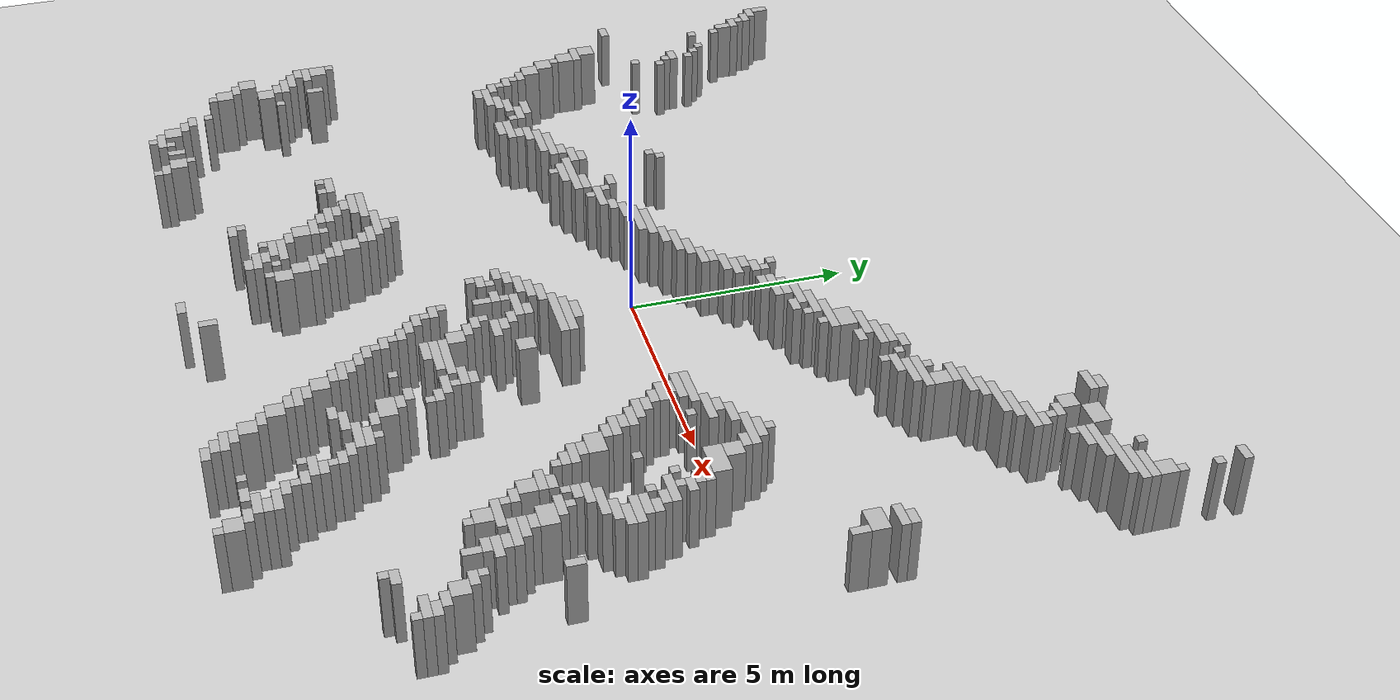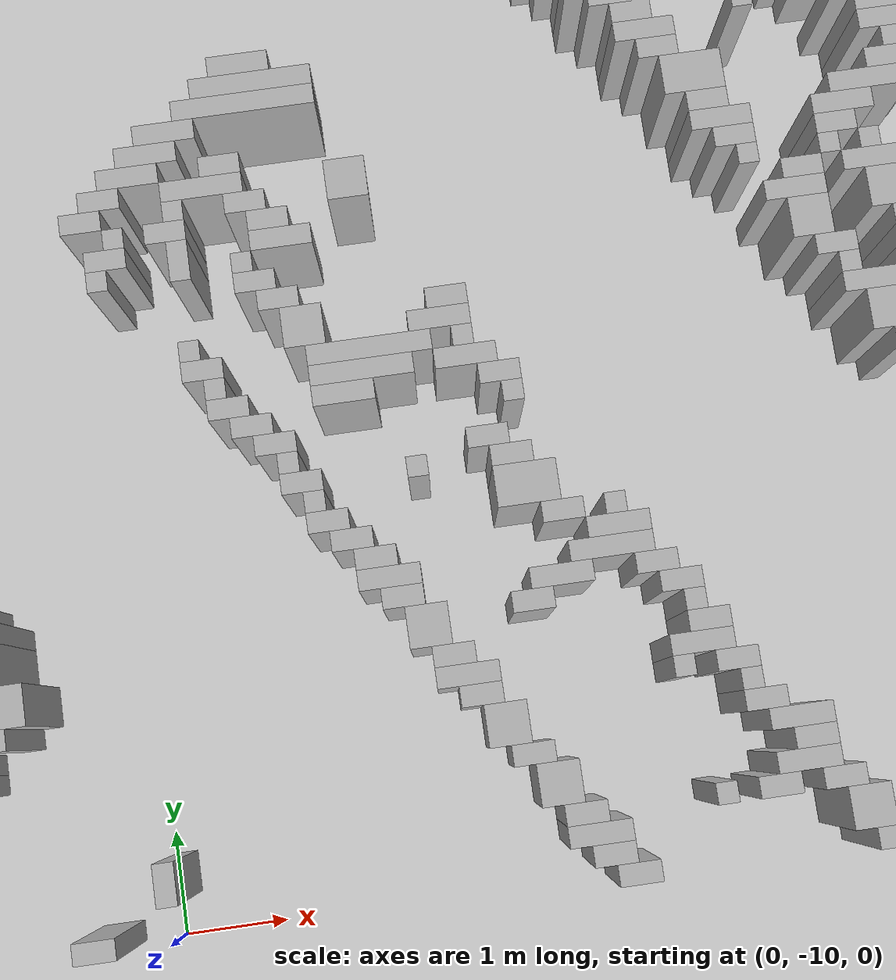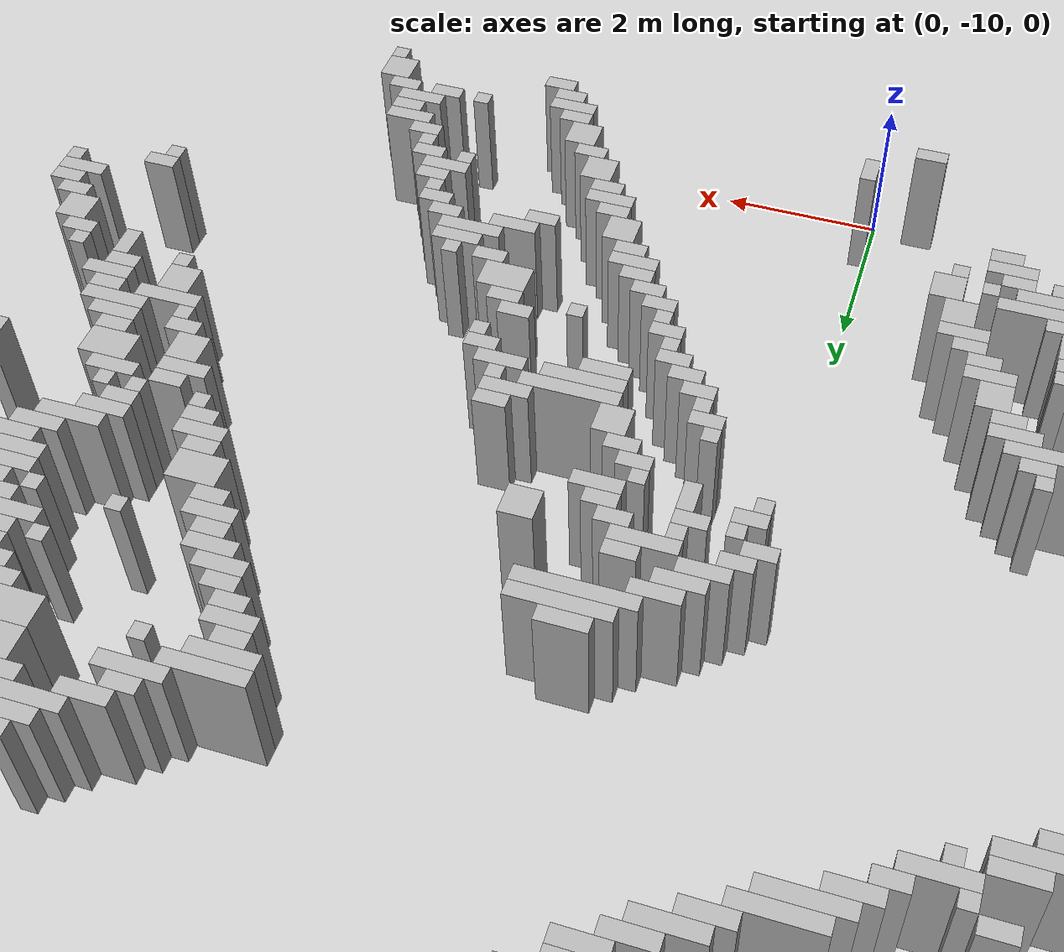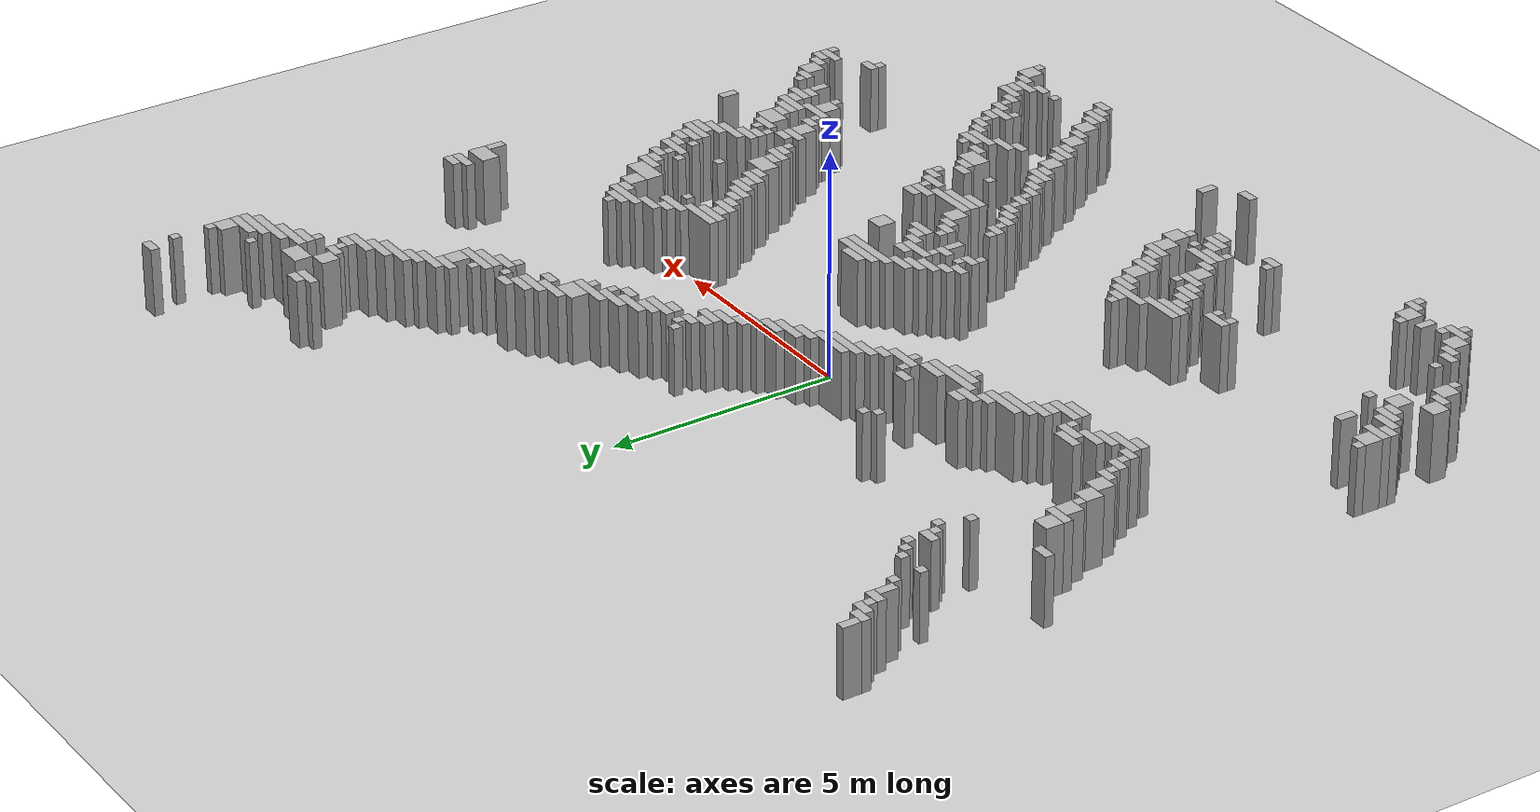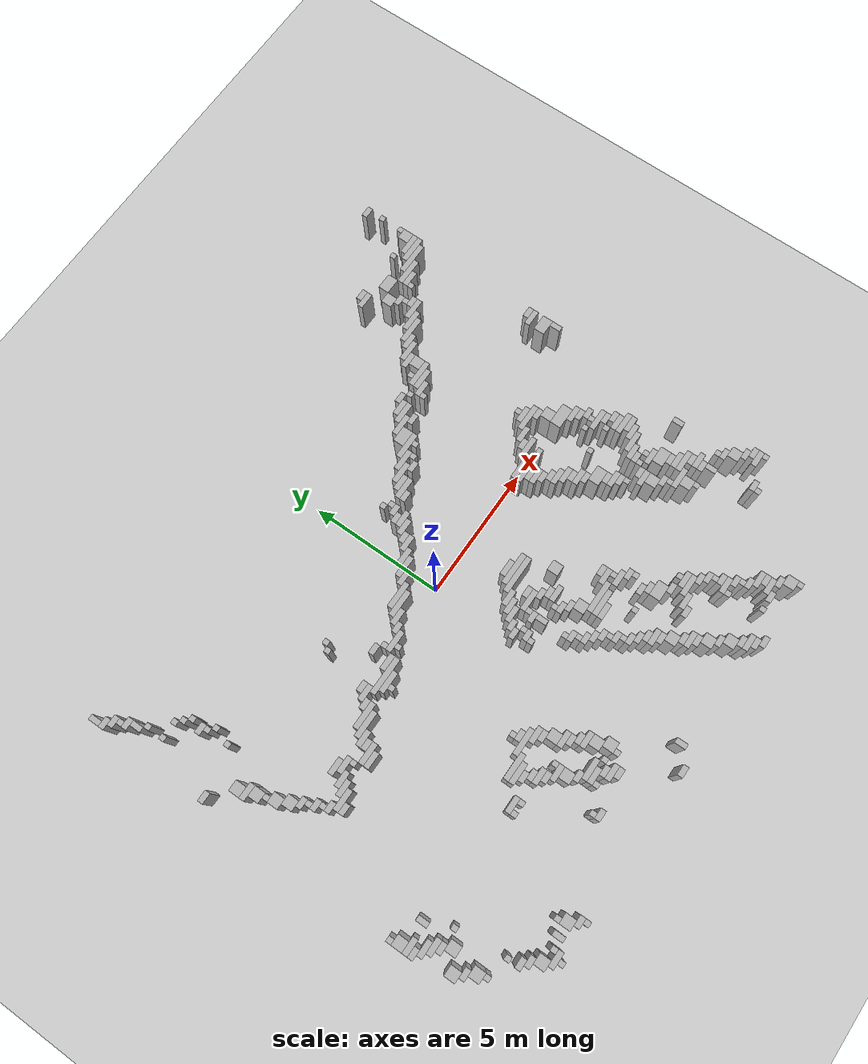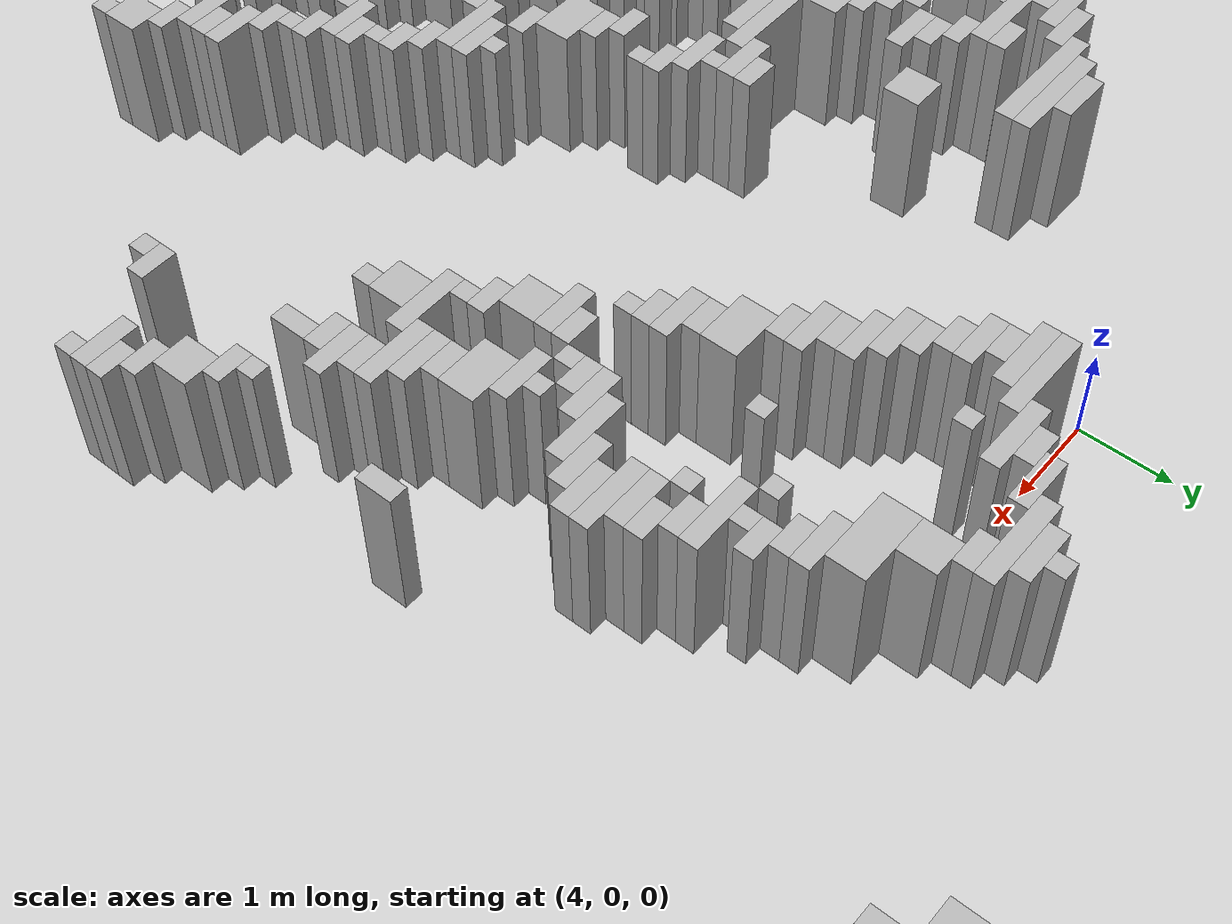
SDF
<?xml version="1.0"?>
<sdf version="1.6">
  <world name="real_map">
    <physics type="ode"><real_time_update_rate>1000</real_time_update_rate><max_step_size>0.001</max_step_size><real_time_factor>1</real_time_factor></physics>
    <include><uri>model://sun</uri></include>
    <include><uri>model://ground_plane</uri></include>
<model name="w0"><static>true</static><pose>9.90 9.30 0.8 0 0 0</pose><link name="l"><collision name="c"><geometry><box><size>0.20 0.20 1.5</size></box></geometry></collision><visual name="v"><geometry><box><size>0.20 0.20 1.5</size></box></geometry><material><ambient>0.7 0.7 0.7 1</ambient></material></visual></link></model>
<model name="w1"><static>true</static><pose>9.80 9.90 0.8 0 0 0</pose><link name="l"><collision name="c"><geometry><box><size>0.40 0.20 1.5</size></box></geometry></collision><visual name="v"><geometry><box><size>0.40 0.20 1.5</size></box></geometry><material><ambient>0.7 0.7 0.7 1</ambient></material></visual></link></model>
<model name="w2"><static>true</static><pose>-9.10 4.70 0.8 0 0 0</pose><link name="l"><collision name="c"><geometry><box><size>0.20 0.20 1.5</size></box></geometry></collision><visual name="v"><geometry><box><size>0.20 0.20 1.5</size></box></geometry><material><ambient>0.7 0.7 0.7 1</ambient></material></visual></link></model>
<model name="w3"><static>true</static><pose>-8.10 3.70 0.8 0 0 0</pose><link name="l"><collision name="c"><geometry><box><size>0.20 0.20 1.5</size></box></geometry></collision><visual name="v"><geometry><box><size>0.20 0.20 1.5</size></box></geometry><material><ambient>0.7 0.7 0.7 1</ambient></material></visual></link></model>
<model name="w4"><static>true</static><pose>9.80 8.20 0.8 0 0 0</pose><link name="l"><collision name="c"><geometry><box><size>0.40 0.40 1.5</size></box></geometry></collision><visual name="v"><geometry><box><size>0.40 0.40 1.5</size></box></geometry><material><ambient>0.7 0.7 0.7 1</ambient></material></visual></link></model>
<model name="w5"><static>true</static><pose>-8.10 3.10 0.8 0 0 0</pose><link name="l"><collision name="c"><geometry><box><size>0.20 0.20 1.5</size></box></geometry></collision><visual name="v"><geometry><box><size>0.20 0.20 1.5</size></box></geometry><material><ambient>0.7 0.7 0.7 1</ambient></material></visual></link></model>
<model name="w6"><static>true</static><pose>9.70 2.70 0.8 0 0 0</pose><link name="l"><collision name="c"><geometry><box><size>0.60 0.20 1.5</size></box></geometry></collision><visual name="v"><geometry><box><size>0.60 0.20 1.5</size></box></geometry><material><ambient>0.7 0.7 0.7 1</ambient></material></visual></link></model>
<model name="w7"><static>true</static><pose>-9.80 5.90 0.8 0 0 0</pose><link name="l"><collision name="c"><geometry><box><size>0.40 0.20 1.5</size></box></geometry></collision><visual name="v"><geometry><box><size>0.40 0.20 1.5</size></box></geometry><material><ambient>0.7 0.7 0.7 1</ambient></material></visual></link></model>
<model name="w8"><static>true</static><pose>9.90 8.50 0.8 0 0 0</pose><link name="l"><collision name="c"><geometry><box><size>0.20 0.20 1.5</size></box></geometry></collision><visual name="v"><geometry><box><size>0.20 0.20 1.5</size></box></geometry><material><ambient>0.7 0.7 0.7 1</ambient></material></visual></link></model>
<model name="w9"><static>true</static><pose>6.50 5.70 0.8 0 0 0</pose><link name="l"><collision name="c"><geometry><box><size>0.60 0.20 1.5</size></box></geometry></collision><visual name="v"><geometry><box><size>0.60 0.20 1.5</size></box></geometry><material><ambient>0.7 0.7 0.7 1</ambient></material></visual></link></model>
<model name="w10"><static>true</static><pose>5.90 5.30 0.8 0 0 0</pose><link name="l"><collision name="c"><geometry><box><size>0.60 0.20 1.5</size></box></geometry></collision><visual name="v"><geometry><box><size>0.60 0.20 1.5</size></box></geometry><material><ambient>0.7 0.7 0.7 1</ambient></material></visual></link></model>
<model name="w11"><static>true</static><pose>7.00 8.10 0.8 0 0 0</pose><link name="l"><collision name="c"><geometry><box><size>0.40 0.20 1.5</size></box></geometry></collision><visual name="v"><geometry><box><size>0.40 0.20 1.5</size></box></geometry><material><ambient>0.7 0.7 0.7 1</ambient></material></visual></link></model>
<model name="w12"><static>true</static><pose>5.60 4.50 0.8 0 0 0</pose><link name="l"><collision name="c"><geometry><box><size>0.80 0.20 1.5</size></box></geometry></collision><visual name="v"><geometry><box><size>0.80 0.20 1.5</size></box></geometry><material><ambient>0.7 0.7 0.7 1</ambient></material></visual></link></model>
<model name="w13"><static>true</static><pose>7.20 6.10 0.8 0 0 0</pose><link name="l"><collision name="c"><geometry><box><size>0.80 0.20 1.5</size></box></geometry></collision><visual name="v"><geometry><box><size>0.80 0.20 1.5</size></box></geometry><material><ambient>0.7 0.7 0.7 1</ambient></material></visual></link></model>
<model name="w14"><static>true</static><pose>-8.20 3.30 0.8 0 0 0</pose><link name="l"><collision name="c"><geometry><box><size>0.40 0.20 1.5</size></box></geometry></collision><visual name="v"><geometry><box><size>0.40 0.20 1.5</size></box></geometry><material><ambient>0.7 0.7 0.7 1</ambient></material></visual></link></model>
<model name="w15"><static>true</static><pose>7.60 6.90 0.8 0 0 0</pose><link name="l"><collision name="c"><geometry><box><size>0.40 0.20 1.5</size></box></geometry></collision><visual name="v"><geometry><box><size>0.40 0.20 1.5</size></box></geometry><material><ambient>0.7 0.7 0.7 1</ambient></material></visual></link></model>
<model name="w16"><static>true</static><pose>-8.10 2.30 0.8 0 0 0</pose><link name="l"><collision name="c"><geometry><box><size>0.20 0.20 1.5</size></box></geometry></collision><visual name="v"><geometry><box><size>0.20 0.20 1.5</size></box></geometry><material><ambient>0.7 0.7 0.7 1</ambient></material></visual></link></model>
<model name="w17"><static>true</static><pose>-3.70 1.70 0.8 0 0 0</pose><link name="l"><collision name="c"><geometry><box><size>0.20 0.20 1.5</size></box></geometry></collision><visual name="v"><geometry><box><size>0.20 0.20 1.5</size></box></geometry><material><ambient>0.7 0.7 0.7 1</ambient></material></visual></link></model>
<model name="w18"><static>true</static><pose>7.80 6.50 0.8 0 0 0</pose><link name="l"><collision name="c"><geometry><box><size>0.40 0.20 1.5</size></box></geometry></collision><visual name="v"><geometry><box><size>0.40 0.20 1.5</size></box></geometry><material><ambient>0.7 0.7 0.7 1</ambient></material></visual></link></model>
<model name="w19"><static>true</static><pose>7.70 6.70 0.8 0 0 0</pose><link name="l"><collision name="c"><geometry><box><size>0.20 0.20 1.5</size></box></geometry></collision><visual name="v"><geometry><box><size>0.20 0.20 1.5</size></box></geometry><material><ambient>0.7 0.7 0.7 1</ambient></material></visual></link></model>
<model name="w20"><static>true</static><pose>-7.90 2.90 0.8 0 0 0</pose><link name="l"><collision name="c"><geometry><box><size>0.20 0.20 1.5</size></box></geometry></collision><visual name="v"><geometry><box><size>0.20 0.20 1.5</size></box></geometry><material><ambient>0.7 0.7 0.7 1</ambient></material></visual></link></model>
<model name="w21"><static>true</static><pose>5.30 4.30 0.8 0 0 0</pose><link name="l"><collision name="c"><geometry><box><size>0.60 0.20 1.5</size></box></geometry></collision><visual name="v"><geometry><box><size>0.60 0.20 1.5</size></box></geometry><material><ambient>0.7 0.7 0.7 1</ambient></material></visual></link></model>
<model name="w22"><static>true</static><pose>5.60 0.30 0.8 0 0 0</pose><link name="l"><collision name="c"><geometry><box><size>0.40 0.20 1.5</size></box></geometry></collision><visual name="v"><geometry><box><size>0.40 0.20 1.5</size></box></geometry><material><ambient>0.7 0.7 0.7 1</ambient></material></visual></link></model>
<model name="w23"><static>true</static><pose>7.70 -1.10 0.8 0 0 0</pose><link name="l"><collision name="c"><geometry><box><size>0.20 0.20 1.5</size></box></geometry></collision><visual name="v"><geometry><box><size>0.20 0.20 1.5</size></box></geometry><material><ambient>0.7 0.7 0.7 1</ambient></material></visual></link></model>
<model name="w24"><static>true</static><pose>0.90 1.90 0.8 0 0 0</pose><link name="l"><collision name="c"><geometry><box><size>0.60 0.20 1.5</size></box></geometry></collision><visual name="v"><geometry><box><size>0.60 0.20 1.5</size></box></geometry><material><ambient>0.7 0.7 0.7 1</ambient></material></visual></link></model>
<model name="w25"><static>true</static><pose>8.10 -1.90 0.8 0 0 0</pose><link name="l"><collision name="c"><geometry><box><size>0.60 0.20 1.5</size></box></geometry></collision><visual name="v"><geometry><box><size>0.60 0.20 1.5</size></box></geometry><material><ambient>0.7 0.7 0.7 1</ambient></material></visual></link></model>
<model name="w26"><static>true</static><pose>0.50 1.50 0.8 0 0 0</pose><link name="l"><collision name="c"><geometry><box><size>0.60 0.20 1.5</size></box></geometry></collision><visual name="v"><geometry><box><size>0.60 0.20 1.5</size></box></geometry><material><ambient>0.7 0.7 0.7 1</ambient></material></visual></link></model>
<model name="w27"><static>true</static><pose>7.80 -1.30 0.8 0 0 0</pose><link name="l"><collision name="c"><geometry><box><size>0.80 0.20 1.5</size></box></geometry></collision><visual name="v"><geometry><box><size>0.80 0.20 1.5</size></box></geometry><material><ambient>0.7 0.7 0.7 1</ambient></material></visual></link></model>
<model name="w28"><static>true</static><pose>7.50 -0.50 0.8 0 0 0</pose><link name="l"><collision name="c"><geometry><box><size>0.60 0.20 1.5</size></box></geometry></collision><visual name="v"><geometry><box><size>0.60 0.20 1.5</size></box></geometry><material><ambient>0.7 0.7 0.7 1</ambient></material></visual></link></model>
<model name="w29"><static>true</static><pose>7.40 7.20 0.8 0 0 0</pose><link name="l"><collision name="c"><geometry><box><size>0.40 0.40 1.5</size></box></geometry></collision><visual name="v"><geometry><box><size>0.40 0.40 1.5</size></box></geometry><material><ambient>0.7 0.7 0.7 1</ambient></material></visual></link></model>
<model name="w30"><static>true</static><pose>1.80 2.50 0.8 0 0 0</pose><link name="l"><collision name="c"><geometry><box><size>0.40 0.20 1.5</size></box></geometry></collision><visual name="v"><geometry><box><size>0.40 0.20 1.5</size></box></geometry><material><ambient>0.7 0.7 0.7 1</ambient></material></visual></link></model>
<model name="w31"><static>true</static><pose>6.50 1.10 0.8 0 0 0</pose><link name="l"><collision name="c"><geometry><box><size>0.20 0.20 1.5</size></box></geometry></collision><visual name="v"><geometry><box><size>0.20 0.20 1.5</size></box></geometry><material><ambient>0.7 0.7 0.7 1</ambient></material></visual></link></model>
<model name="w32"><static>true</static><pose>7.30 -1.10 0.8 0 0 0</pose><link name="l"><collision name="c"><geometry><box><size>0.20 0.20 1.5</size></box></geometry></collision><visual name="v"><geometry><box><size>0.20 0.20 1.5</size></box></geometry><material><ambient>0.7 0.7 0.7 1</ambient></material></visual></link></model>
<model name="w33"><static>true</static><pose>7.70 -1.70 0.8 0 0 0</pose><link name="l"><collision name="c"><geometry><box><size>0.20 0.20 1.5</size></box></geometry></collision><visual name="v"><geometry><box><size>0.20 0.20 1.5</size></box></geometry><material><ambient>0.7 0.7 0.7 1</ambient></material></visual></link></model>
<model name="w34"><static>true</static><pose>0.20 -2.90 0.8 0 0 0</pose><link name="l"><collision name="c"><geometry><box><size>0.40 0.20 1.5</size></box></geometry></collision><visual name="v"><geometry><box><size>0.40 0.20 1.5</size></box></geometry><material><ambient>0.7 0.7 0.7 1</ambient></material></visual></link></model>
<model name="w35"><static>true</static><pose>0.90 -3.10 0.8 0 0 0</pose><link name="l"><collision name="c"><geometry><box><size>0.20 0.20 1.5</size></box></geometry></collision><visual name="v"><geometry><box><size>0.20 0.20 1.5</size></box></geometry><material><ambient>0.7 0.7 0.7 1</ambient></material></visual></link></model>
<model name="w36"><static>true</static><pose>7.00 0.20 0.8 0 0 0</pose><link name="l"><collision name="c"><geometry><box><size>0.40 0.40 1.5</size></box></geometry></collision><visual name="v"><geometry><box><size>0.40 0.40 1.5</size></box></geometry><material><ambient>0.7 0.7 0.7 1</ambient></material></visual></link></model>
<model name="w37"><static>true</static><pose>6.90 7.90 0.8 0 0 0</pose><link name="l"><collision name="c"><geometry><box><size>0.60 0.20 1.5</size></box></geometry></collision><visual name="v"><geometry><box><size>0.60 0.20 1.5</size></box></geometry><material><ambient>0.7 0.7 0.7 1</ambient></material></visual></link></model>
<model name="w38"><static>true</static><pose>7.90 7.60 0.8 0 0 0</pose><link name="l"><collision name="c"><geometry><box><size>0.60 0.40 1.5</size></box></geometry></collision><visual name="v"><geometry><box><size>0.60 0.40 1.5</size></box></geometry><material><ambient>0.7 0.7 0.7 1</ambient></material></visual></link></model>
<model name="w39"><static>true</static><pose>1.60 -3.10 0.8 0 0 0</pose><link name="l"><collision name="c"><geometry><box><size>0.40 0.20 1.5</size></box></geometry></collision><visual name="v"><geometry><box><size>0.40 0.20 1.5</size></box></geometry><material><ambient>0.7 0.7 0.7 1</ambient></material></visual></link></model>
<model name="w40"><static>true</static><pose>7.00 -3.50 0.8 0 0 0</pose><link name="l"><collision name="c"><geometry><box><size>0.40 0.20 1.5</size></box></geometry></collision><visual name="v"><geometry><box><size>0.40 0.20 1.5</size></box></geometry><material><ambient>0.7 0.7 0.7 1</ambient></material></visual></link></model>
<model name="w41"><static>true</static><pose>1.80 -3.30 0.8 0 0 0</pose><link name="l"><collision name="c"><geometry><box><size>0.40 0.20 1.5</size></box></geometry></collision><visual name="v"><geometry><box><size>0.40 0.20 1.5</size></box></geometry><material><ambient>0.7 0.7 0.7 1</ambient></material></visual></link></model>
<model name="w42"><static>true</static><pose>8.00 -1.50 0.8 0 0 0</pose><link name="l"><collision name="c"><geometry><box><size>0.40 0.20 1.5</size></box></geometry></collision><visual name="v"><geometry><box><size>0.40 0.20 1.5</size></box></geometry><material><ambient>0.7 0.7 0.7 1</ambient></material></visual></link></model>
<model name="w43"><static>true</static><pose>8.10 -2.50 0.8 0 0 0</pose><link name="l"><collision name="c"><geometry><box><size>0.60 0.20 1.5</size></box></geometry></collision><visual name="v"><geometry><box><size>0.60 0.20 1.5</size></box></geometry><material><ambient>0.7 0.7 0.7 1</ambient></material></visual></link></model>
<model name="w44"><static>true</static><pose>0.90 -3.60 0.8 0 0 0</pose><link name="l"><collision name="c"><geometry><box><size>0.20 0.40 1.5</size></box></geometry></collision><visual name="v"><geometry><box><size>0.20 0.40 1.5</size></box></geometry><material><ambient>0.7 0.7 0.7 1</ambient></material></visual></link></model>
<model name="w45"><static>true</static><pose>7.30 -3.30 0.8 0 0 0</pose><link name="l"><collision name="c"><geometry><box><size>0.20 0.20 1.5</size></box></geometry></collision><visual name="v"><geometry><box><size>0.20 0.20 1.5</size></box></geometry><material><ambient>0.7 0.7 0.7 1</ambient></material></visual></link></model>
<model name="w46"><static>true</static><pose>8.20 -2.10 0.8 0 0 0</pose><link name="l"><collision name="c"><geometry><box><size>0.80 0.20 1.5</size></box></geometry></collision><visual name="v"><geometry><box><size>0.80 0.20 1.5</size></box></geometry><material><ambient>0.7 0.7 0.7 1</ambient></material></visual></link></model>
<model name="w47"><static>true</static><pose>1.00 2.30 0.8 0 0 0</pose><link name="l"><collision name="c"><geometry><box><size>0.40 0.20 1.5</size></box></geometry></collision><visual name="v"><geometry><box><size>0.40 0.20 1.5</size></box></geometry><material><ambient>0.7 0.7 0.7 1</ambient></material></visual></link></model>
<model name="w48"><static>true</static><pose>3.50 3.30 0.8 0 0 0</pose><link name="l"><collision name="c"><geometry><box><size>0.20 0.20 1.5</size></box></geometry></collision><visual name="v"><geometry><box><size>0.20 0.20 1.5</size></box></geometry><material><ambient>0.7 0.7 0.7 1</ambient></material></visual></link></model>
<model name="w49"><static>true</static><pose>7.60 6.30 0.8 0 0 0</pose><link name="l"><collision name="c"><geometry><box><size>0.80 0.20 1.5</size></box></geometry></collision><visual name="v"><geometry><box><size>0.80 0.20 1.5</size></box></geometry><material><ambient>0.7 0.7 0.7 1</ambient></material></visual></link></model>
<model name="w50"><static>true</static><pose>-2.70 0.10 0.8 0 0 0</pose><link name="l"><collision name="c"><geometry><box><size>0.20 0.20 1.5</size></box></geometry></collision><visual name="v"><geometry><box><size>0.20 0.20 1.5</size></box></geometry><material><ambient>0.7 0.7 0.7 1</ambient></material></visual></link></model>
<model name="w51"><static>true</static><pose>1.10 2.90 0.8 0 0 0</pose><link name="l"><collision name="c"><geometry><box><size>0.20 0.20 1.5</size></box></geometry></collision><visual name="v"><geometry><box><size>0.20 0.20 1.5</size></box></geometry><material><ambient>0.7 0.7 0.7 1</ambient></material></visual></link></model>
<model name="w52"><static>true</static><pose>3.50 3.80 0.8 0 0 0</pose><link name="l"><collision name="c"><geometry><box><size>0.60 0.40 1.5</size></box></geometry></collision><visual name="v"><geometry><box><size>0.60 0.40 1.5</size></box></geometry><material><ambient>0.7 0.7 0.7 1</ambient></material></visual></link></model>
<model name="w53"><static>true</static><pose>7.60 -0.70 0.8 0 0 0</pose><link name="l"><collision name="c"><geometry><box><size>0.40 0.20 1.5</size></box></geometry></collision><visual name="v"><geometry><box><size>0.40 0.20 1.5</size></box></geometry><material><ambient>0.7 0.7 0.7 1</ambient></material></visual></link></model>
<model name="w54"><static>true</static><pose>8.50 7.10 0.8 0 0 0</pose><link name="l"><collision name="c"><geometry><box><size>0.60 0.20 1.5</size></box></geometry></collision><visual name="v"><geometry><box><size>0.60 0.20 1.5</size></box></geometry><material><ambient>0.7 0.7 0.7 1</ambient></material></visual></link></model>
<model name="w55"><static>true</static><pose>1.20 2.50 0.8 0 0 0</pose><link name="l"><collision name="c"><geometry><box><size>0.40 0.20 1.5</size></box></geometry></collision><visual name="v"><geometry><box><size>0.40 0.20 1.5</size></box></geometry><material><ambient>0.7 0.7 0.7 1</ambient></material></visual></link></model>
<model name="w56"><static>true</static><pose>8.40 -4.70 0.8 0 0 0</pose><link name="l"><collision name="c"><geometry><box><size>0.40 0.20 1.5</size></box></geometry></collision><visual name="v"><geometry><box><size>0.40 0.20 1.5</size></box></geometry><material><ambient>0.7 0.7 0.7 1</ambient></material></visual></link></model>
<model name="w57"><static>true</static><pose>-9.90 6.20 0.8 0 0 0</pose><link name="l"><collision name="c"><geometry><box><size>0.20 0.40 1.5</size></box></geometry></collision><visual name="v"><geometry><box><size>0.20 0.40 1.5</size></box></geometry><material><ambient>0.7 0.7 0.7 1</ambient></material></visual></link></model>
<model name="w58"><static>true</static><pose>1.40 -2.70 0.8 0 0 0</pose><link name="l"><collision name="c"><geometry><box><size>0.40 0.20 1.5</size></box></geometry></collision><visual name="v"><geometry><box><size>0.40 0.20 1.5</size></box></geometry><material><ambient>0.7 0.7 0.7 1</ambient></material></visual></link></model>
<model name="w59"><static>true</static><pose>7.70 -3.30 0.8 0 0 0</pose><link name="l"><collision name="c"><geometry><box><size>0.20 0.20 1.5</size></box></geometry></collision><visual name="v"><geometry><box><size>0.20 0.20 1.5</size></box></geometry><material><ambient>0.7 0.7 0.7 1</ambient></material></visual></link></model>
<model name="w60"><static>true</static><pose>-9.80 1.90 0.8 0 0 0</pose><link name="l"><collision name="c"><geometry><box><size>0.40 0.20 1.5</size></box></geometry></collision><visual name="v"><geometry><box><size>0.40 0.20 1.5</size></box></geometry><material><ambient>0.7 0.7 0.7 1</ambient></material></visual></link></model>
<model name="w61"><static>true</static><pose>1.60 -3.90 0.8 0 0 0</pose><link name="l"><collision name="c"><geometry><box><size>0.40 0.20 1.5</size></box></geometry></collision><visual name="v"><geometry><box><size>0.40 0.20 1.5</size></box></geometry><material><ambient>0.7 0.7 0.7 1</ambient></material></visual></link></model>
<model name="w62"><static>true</static><pose>-3.60 -0.70 0.8 0 0 0</pose><link name="l"><collision name="c"><geometry><box><size>0.80 0.20 1.5</size></box></geometry></collision><visual name="v"><geometry><box><size>0.80 0.20 1.5</size></box></geometry><material><ambient>0.7 0.7 0.7 1</ambient></material></visual></link></model>
<model name="w63"><static>true</static><pose>-2.00 0.10 0.8 0 0 0</pose><link name="l"><collision name="c"><geometry><box><size>0.40 0.20 1.5</size></box></geometry></collision><visual name="v"><geometry><box><size>0.40 0.20 1.5</size></box></geometry><material><ambient>0.7 0.7 0.7 1</ambient></material></visual></link></model>
<model name="w64"><static>true</static><pose>1.80 -4.10 0.8 0 0 0</pose><link name="l"><collision name="c"><geometry><box><size>0.40 0.20 1.5</size></box></geometry></collision><visual name="v"><geometry><box><size>0.40 0.20 1.5</size></box></geometry><material><ambient>0.7 0.7 0.7 1</ambient></material></visual></link></model>
<model name="w65"><static>true</static><pose>3.80 -5.10 0.8 0 0 0</pose><link name="l"><collision name="c"><geometry><box><size>0.40 0.20 1.5</size></box></geometry></collision><visual name="v"><geometry><box><size>0.40 0.20 1.5</size></box></geometry><material><ambient>0.7 0.7 0.7 1</ambient></material></visual></link></model>
<model name="w66"><static>true</static><pose>-9.80 -5.60 0.8 0 0 0</pose><link name="l"><collision name="c"><geometry><box><size>0.40 0.40 1.5</size></box></geometry></collision><visual name="v"><geometry><box><size>0.40 0.40 1.5</size></box></geometry><material><ambient>0.7 0.7 0.7 1</ambient></material></visual></link></model>
<model name="w67"><static>true</static><pose>2.00 -4.40 0.8 0 0 0</pose><link name="l"><collision name="c"><geometry><box><size>0.40 0.40 1.5</size></box></geometry></collision><visual name="v"><geometry><box><size>0.40 0.40 1.5</size></box></geometry><material><ambient>0.7 0.7 0.7 1</ambient></material></visual></link></model>
<model name="w68"><static>true</static><pose>9.80 2.90 0.8 0 0 0</pose><link name="l"><collision name="c"><geometry><box><size>0.40 0.20 1.5</size></box></geometry></collision><visual name="v"><geometry><box><size>0.40 0.20 1.5</size></box></geometry><material><ambient>0.7 0.7 0.7 1</ambient></material></visual></link></model>
<model name="w69"><static>true</static><pose>-2.70 -4.90 0.8 0 0 0</pose><link name="l"><collision name="c"><geometry><box><size>0.20 0.20 1.5</size></box></geometry></collision><visual name="v"><geometry><box><size>0.20 0.20 1.5</size></box></geometry><material><ambient>0.7 0.7 0.7 1</ambient></material></visual></link></model>
<model name="w70"><static>true</static><pose>4.20 3.90 0.8 0 0 0</pose><link name="l"><collision name="c"><geometry><box><size>0.40 0.20 1.5</size></box></geometry></collision><visual name="v"><geometry><box><size>0.40 0.20 1.5</size></box></geometry><material><ambient>0.7 0.7 0.7 1</ambient></material></visual></link></model>
<model name="w71"><static>true</static><pose>9.70 2.20 0.8 0 0 0</pose><link name="l"><collision name="c"><geometry><box><size>0.60 0.40 1.5</size></box></geometry></collision><visual name="v"><geometry><box><size>0.60 0.40 1.5</size></box></geometry><material><ambient>0.7 0.7 0.7 1</ambient></material></visual></link></model>
<model name="w72"><static>true</static><pose>-8.50 4.10 0.8 0 0 0</pose><link name="l"><collision name="c"><geometry><box><size>0.20 0.20 1.5</size></box></geometry></collision><visual name="v"><geometry><box><size>0.20 0.20 1.5</size></box></geometry><material><ambient>0.7 0.7 0.7 1</ambient></material></visual></link></model>
<model name="w73"><static>true</static><pose>9.90 1.80 0.8 0 0 0</pose><link name="l"><collision name="c"><geometry><box><size>0.20 0.40 1.5</size></box></geometry></collision><visual name="v"><geometry><box><size>0.20 0.40 1.5</size></box></geometry><material><ambient>0.7 0.7 0.7 1</ambient></material></visual></link></model>
<model name="w74"><static>true</static><pose>-9.00 1.20 0.8 0 0 0</pose><link name="l"><collision name="c"><geometry><box><size>0.40 0.40 1.5</size></box></geometry></collision><visual name="v"><geometry><box><size>0.40 0.40 1.5</size></box></geometry><material><ambient>0.7 0.7 0.7 1</ambient></material></visual></link></model>
<model name="w75"><static>true</static><pose>2.60 -3.00 0.8 0 0 0</pose><link name="l"><collision name="c"><geometry><box><size>0.40 0.40 1.5</size></box></geometry></collision><visual name="v"><geometry><box><size>0.40 0.40 1.5</size></box></geometry><material><ambient>0.7 0.7 0.7 1</ambient></material></visual></link></model>
<model name="w76"><static>true</static><pose>5.00 -0.90 0.8 0 0 0</pose><link name="l"><collision name="c"><geometry><box><size>0.40 0.20 1.5</size></box></geometry></collision><visual name="v"><geometry><box><size>0.40 0.20 1.5</size></box></geometry><material><ambient>0.7 0.7 0.7 1</ambient></material></visual></link></model>
<model name="w77"><static>true</static><pose>-9.60 5.70 0.8 0 0 0</pose><link name="l"><collision name="c"><geometry><box><size>0.40 0.20 1.5</size></box></geometry></collision><visual name="v"><geometry><box><size>0.40 0.20 1.5</size></box></geometry><material><ambient>0.7 0.7 0.7 1</ambient></material></visual></link></model>
<model name="w78"><static>true</static><pose>-2.60 -5.10 0.8 0 0 0</pose><link name="l"><collision name="c"><geometry><box><size>0.40 0.20 1.5</size></box></geometry></collision><visual name="v"><geometry><box><size>0.40 0.20 1.5</size></box></geometry><material><ambient>0.7 0.7 0.7 1</ambient></material></visual></link></model>
<model name="w79"><static>true</static><pose>2.80 2.90 0.8 0 0 0</pose><link name="l"><collision name="c"><geometry><box><size>0.40 0.20 1.5</size></box></geometry></collision><visual name="v"><geometry><box><size>0.40 0.20 1.5</size></box></geometry><material><ambient>0.7 0.7 0.7 1</ambient></material></visual></link></model>
<model name="w80"><static>true</static><pose>3.80 -5.90 0.8 0 0 0</pose><link name="l"><collision name="c"><geometry><box><size>0.40 0.20 1.5</size></box></geometry></collision><visual name="v"><geometry><box><size>0.40 0.20 1.5</size></box></geometry><material><ambient>0.7 0.7 0.7 1</ambient></material></visual></link></model>
<model name="w81"><static>true</static><pose>5.20 -1.10 0.8 0 0 0</pose><link name="l"><collision name="c"><geometry><box><size>0.40 0.20 1.5</size></box></geometry></collision><visual name="v"><geometry><box><size>0.40 0.20 1.5</size></box></geometry><material><ambient>0.7 0.7 0.7 1</ambient></material></visual></link></model>
<model name="w82"><static>true</static><pose>-9.40 5.30 0.8 0 0 0</pose><link name="l"><collision name="c"><geometry><box><size>0.40 0.20 1.5</size></box></geometry></collision><visual name="v"><geometry><box><size>0.40 0.20 1.5</size></box></geometry><material><ambient>0.7 0.7 0.7 1</ambient></material></visual></link></model>
<model name="w83"><static>true</static><pose>-2.30 -5.50 0.8 0 0 0</pose><link name="l"><collision name="c"><geometry><box><size>0.60 0.20 1.5</size></box></geometry></collision><visual name="v"><geometry><box><size>0.60 0.20 1.5</size></box></geometry><material><ambient>0.7 0.7 0.7 1</ambient></material></visual></link></model>
<model name="w84"><static>true</static><pose>-9.20 -6.70 0.8 0 0 0</pose><link name="l"><collision name="c"><geometry><box><size>0.40 0.20 1.5</size></box></geometry></collision><visual name="v"><geometry><box><size>0.40 0.20 1.5</size></box></geometry><material><ambient>0.7 0.7 0.7 1</ambient></material></visual></link></model>
<model name="w85"><static>true</static><pose>-2.50 -0.30 0.8 0 0 0</pose><link name="l"><collision name="c"><geometry><box><size>0.20 0.20 1.5</size></box></geometry></collision><visual name="v"><geometry><box><size>0.20 0.20 1.5</size></box></geometry><material><ambient>0.7 0.7 0.7 1</ambient></material></visual></link></model>
<model name="w86"><static>true</static><pose>-2.00 -6.00 0.8 0 0 0</pose><link name="l"><collision name="c"><geometry><box><size>0.40 0.40 1.5</size></box></geometry></collision><visual name="v"><geometry><box><size>0.40 0.40 1.5</size></box></geometry><material><ambient>0.7 0.7 0.7 1</ambient></material></visual></link></model>
<model name="w87"><static>true</static><pose>5.30 -1.30 0.8 0 0 0</pose><link name="l"><collision name="c"><geometry><box><size>0.60 0.20 1.5</size></box></geometry></collision><visual name="v"><geometry><box><size>0.60 0.20 1.5</size></box></geometry><material><ambient>0.7 0.7 0.7 1</ambient></material></visual></link></model>
<model name="w88"><static>true</static><pose>-1.90 -6.30 0.8 0 0 0</pose><link name="l"><collision name="c"><geometry><box><size>0.60 0.20 1.5</size></box></geometry></collision><visual name="v"><geometry><box><size>0.60 0.20 1.5</size></box></geometry><material><ambient>0.7 0.7 0.7 1</ambient></material></visual></link></model>
<model name="w89"><static>true</static><pose>5.10 4.10 0.8 0 0 0</pose><link name="l"><collision name="c"><geometry><box><size>0.20 0.20 1.5</size></box></geometry></collision><visual name="v"><geometry><box><size>0.20 0.20 1.5</size></box></geometry><material><ambient>0.7 0.7 0.7 1</ambient></material></visual></link></model>
<model name="w90"><static>true</static><pose>5.60 -1.70 0.8 0 0 0</pose><link name="l"><collision name="c"><geometry><box><size>0.40 0.20 1.5</size></box></geometry></collision><visual name="v"><geometry><box><size>0.40 0.20 1.5</size></box></geometry><material><ambient>0.7 0.7 0.7 1</ambient></material></visual></link></model>
<model name="w91"><static>true</static><pose>-9.10 4.10 0.8 0 0 0</pose><link name="l"><collision name="c"><geometry><box><size>0.20 0.20 1.5</size></box></geometry></collision><visual name="v"><geometry><box><size>0.20 0.20 1.5</size></box></geometry><material><ambient>0.7 0.7 0.7 1</ambient></material></visual></link></model>
<model name="w92"><static>true</static><pose>-1.80 -6.50 0.8 0 0 0</pose><link name="l"><collision name="c"><geometry><box><size>0.40 0.20 1.5</size></box></geometry></collision><visual name="v"><geometry><box><size>0.40 0.20 1.5</size></box></geometry><material><ambient>0.7 0.7 0.7 1</ambient></material></visual></link></model>
<model name="w93"><static>true</static><pose>3.40 -4.30 0.8 0 0 0</pose><link name="l"><collision name="c"><geometry><box><size>0.40 0.20 1.5</size></box></geometry></collision><visual name="v"><geometry><box><size>0.40 0.20 1.5</size></box></geometry><material><ambient>0.7 0.7 0.7 1</ambient></material></visual></link></model>
<model name="w94"><static>true</static><pose>5.70 -0.30 0.8 0 0 0</pose><link name="l"><collision name="c"><geometry><box><size>0.20 0.20 1.5</size></box></geometry></collision><visual name="v"><geometry><box><size>0.20 0.20 1.5</size></box></geometry><material><ambient>0.7 0.7 0.7 1</ambient></material></visual></link></model>
<model name="w95"><static>true</static><pose>-8.30 3.90 0.8 0 0 0</pose><link name="l"><collision name="c"><geometry><box><size>0.20 0.20 1.5</size></box></geometry></collision><visual name="v"><geometry><box><size>0.20 0.20 1.5</size></box></geometry><material><ambient>0.7 0.7 0.7 1</ambient></material></visual></link></model>
<model name="w96"><static>true</static><pose>-3.20 -6.50 0.8 0 0 0</pose><link name="l"><collision name="c"><geometry><box><size>0.40 0.20 1.5</size></box></geometry></collision><visual name="v"><geometry><box><size>0.40 0.20 1.5</size></box></geometry><material><ambient>0.7 0.7 0.7 1</ambient></material></visual></link></model>
<model name="w97"><static>true</static><pose>5.80 -2.10 0.8 0 0 0</pose><link name="l"><collision name="c"><geometry><box><size>0.40 0.20 1.5</size></box></geometry></collision><visual name="v"><geometry><box><size>0.40 0.20 1.5</size></box></geometry><material><ambient>0.7 0.7 0.7 1</ambient></material></visual></link></model>
<model name="w98"><static>true</static><pose>3.60 -5.70 0.8 0 0 0</pose><link name="l"><collision name="c"><geometry><box><size>0.40 0.20 1.5</size></box></geometry></collision><visual name="v"><geometry><box><size>0.40 0.20 1.5</size></box></geometry><material><ambient>0.7 0.7 0.7 1</ambient></material></visual></link></model>
<model name="w99"><static>true</static><pose>6.10 -2.40 0.8 0 0 0</pose><link name="l"><collision name="c"><geometry><box><size>0.60 0.40 1.5</size></box></geometry></collision><visual name="v"><geometry><box><size>0.60 0.40 1.5</size></box></geometry><material><ambient>0.7 0.7 0.7 1</ambient></material></visual></link></model>
<model name="w100"><static>true</static><pose>-8.20 -0.70 0.8 0 0 0</pose><link name="l"><collision name="c"><geometry><box><size>0.40 0.20 1.5</size></box></geometry></collision><visual name="v"><geometry><box><size>0.40 0.20 1.5</size></box></geometry><material><ambient>0.7 0.7 0.7 1</ambient></material></visual></link></model>
<model name="w101"><static>true</static><pose>3.80 -7.30 0.8 0 0 0</pose><link name="l"><collision name="c"><geometry><box><size>0.40 0.20 1.5</size></box></geometry></collision><visual name="v"><geometry><box><size>0.40 0.20 1.5</size></box></geometry><material><ambient>0.7 0.7 0.7 1</ambient></material></visual></link></model>
<model name="w102"><static>true</static><pose>6.20 -2.70 0.8 0 0 0</pose><link name="l"><collision name="c"><geometry><box><size>0.40 0.20 1.5</size></box></geometry></collision><visual name="v"><geometry><box><size>0.40 0.20 1.5</size></box></geometry><material><ambient>0.7 0.7 0.7 1</ambient></material></visual></link></model>
<model name="w103"><static>true</static><pose>-8.00 -1.10 0.8 0 0 0</pose><link name="l"><collision name="c"><geometry><box><size>0.40 0.20 1.5</size></box></geometry></collision><visual name="v"><geometry><box><size>0.40 0.20 1.5</size></box></geometry><material><ambient>0.7 0.7 0.7 1</ambient></material></visual></link></model>
<model name="w104"><static>true</static><pose>6.10 -8.70 0.8 0 0 0</pose><link name="l"><collision name="c"><geometry><box><size>0.60 0.20 1.5</size></box></geometry></collision><visual name="v"><geometry><box><size>0.60 0.20 1.5</size></box></geometry><material><ambient>0.7 0.7 0.7 1</ambient></material></visual></link></model>
<model name="w105"><static>true</static><pose>-7.80 -1.50 0.8 0 0 0</pose><link name="l"><collision name="c"><geometry><box><size>0.40 0.20 1.5</size></box></geometry></collision><visual name="v"><geometry><box><size>0.40 0.20 1.5</size></box></geometry><material><ambient>0.7 0.7 0.7 1</ambient></material></visual></link></model>
<model name="w106"><static>true</static><pose>0.10 -3.70 0.8 0 0 0</pose><link name="l"><collision name="c"><geometry><box><size>0.20 0.20 1.5</size></box></geometry></collision><visual name="v"><geometry><box><size>0.20 0.20 1.5</size></box></geometry><material><ambient>0.7 0.7 0.7 1</ambient></material></visual></link></model>
<model name="w107"><static>true</static><pose>5.30 -7.50 0.8 0 0 0</pose><link name="l"><collision name="c"><geometry><box><size>0.20 0.20 1.5</size></box></geometry></collision><visual name="v"><geometry><box><size>0.20 0.20 1.5</size></box></geometry><material><ambient>0.7 0.7 0.7 1</ambient></material></visual></link></model>
<model name="w108"><static>true</static><pose>5.80 -8.50 0.8 0 0 0</pose><link name="l"><collision name="c"><geometry><box><size>0.40 0.20 1.5</size></box></geometry></collision><visual name="v"><geometry><box><size>0.40 0.20 1.5</size></box></geometry><material><ambient>0.7 0.7 0.7 1</ambient></material></visual></link></model>
<model name="w109"><static>true</static><pose>6.40 -3.10 0.8 0 0 0</pose><link name="l"><collision name="c"><geometry><box><size>0.40 0.20 1.5</size></box></geometry></collision><visual name="v"><geometry><box><size>0.40 0.20 1.5</size></box></geometry><material><ambient>0.7 0.7 0.7 1</ambient></material></visual></link></model>
<model name="w110"><static>true</static><pose>4.10 -7.10 0.8 0 0 0</pose><link name="l"><collision name="c"><geometry><box><size>0.60 0.20 1.5</size></box></geometry></collision><visual name="v"><geometry><box><size>0.60 0.20 1.5</size></box></geometry><material><ambient>0.7 0.7 0.7 1</ambient></material></visual></link></model>
<model name="w111"><static>true</static><pose>4.20 -6.50 0.8 0 0 0</pose><link name="l"><collision name="c"><geometry><box><size>0.40 0.20 1.5</size></box></geometry></collision><visual name="v"><geometry><box><size>0.40 0.20 1.5</size></box></geometry><material><ambient>0.7 0.7 0.7 1</ambient></material></visual></link></model>
<model name="w112"><static>true</static><pose>6.70 -1.70 0.8 0 0 0</pose><link name="l"><collision name="c"><geometry><box><size>0.20 0.20 1.5</size></box></geometry></collision><visual name="v"><geometry><box><size>0.20 0.20 1.5</size></box></geometry><material><ambient>0.7 0.7 0.7 1</ambient></material></visual></link></model>
<model name="w113"><static>true</static><pose>9.80 -6.30 0.8 0 0 0</pose><link name="l"><collision name="c"><geometry><box><size>0.40 0.20 1.5</size></box></geometry></collision><visual name="v"><geometry><box><size>0.40 0.20 1.5</size></box></geometry><material><ambient>0.7 0.7 0.7 1</ambient></material></visual></link></model>
<model name="w114"><static>true</static><pose>9.90 -6.70 0.8 0 0 0</pose><link name="l"><collision name="c"><geometry><box><size>0.20 0.20 1.5</size></box></geometry></collision><visual name="v"><geometry><box><size>0.20 0.20 1.5</size></box></geometry><material><ambient>0.7 0.7 0.7 1</ambient></material></visual></link></model>
<model name="w115"><static>true</static><pose>7.00 -4.00 0.8 0 0 0</pose><link name="l"><collision name="c"><geometry><box><size>0.40 0.40 1.5</size></box></geometry></collision><visual name="v"><geometry><box><size>0.40 0.40 1.5</size></box></geometry><material><ambient>0.7 0.7 0.7 1</ambient></material></visual></link></model>
<model name="w116"><static>true</static><pose>8.90 8.10 0.8 0 0 0</pose><link name="l"><collision name="c"><geometry><box><size>0.20 0.20 1.5</size></box></geometry></collision><visual name="v"><geometry><box><size>0.20 0.20 1.5</size></box></geometry><material><ambient>0.7 0.7 0.7 1</ambient></material></visual></link></model>
<model name="w117"><static>true</static><pose>6.90 -3.70 0.8 0 0 0</pose><link name="l"><collision name="c"><geometry><box><size>0.60 0.20 1.5</size></box></geometry></collision><visual name="v"><geometry><box><size>0.60 0.20 1.5</size></box></geometry><material><ambient>0.7 0.7 0.7 1</ambient></material></visual></link></model>
<model name="w118"><static>true</static><pose>9.60 7.90 0.8 0 0 0</pose><link name="l"><collision name="c"><geometry><box><size>0.80 0.20 1.5</size></box></geometry></collision><visual name="v"><geometry><box><size>0.80 0.20 1.5</size></box></geometry><material><ambient>0.7 0.7 0.7 1</ambient></material></visual></link></model>
<model name="w119"><static>true</static><pose>7.90 -3.80 0.8 0 0 0</pose><link name="l"><collision name="c"><geometry><box><size>0.60 0.40 1.5</size></box></geometry></collision><visual name="v"><geometry><box><size>0.60 0.40 1.5</size></box></geometry><material><ambient>0.7 0.7 0.7 1</ambient></material></visual></link></model>
<model name="w120"><static>true</static><pose>9.50 7.70 0.8 0 0 0</pose><link name="l"><collision name="c"><geometry><box><size>1.00 0.20 1.5</size></box></geometry></collision><visual name="v"><geometry><box><size>1.00 0.20 1.5</size></box></geometry><material><ambient>0.7 0.7 0.7 1</ambient></material></visual></link></model>
<model name="w121"><static>true</static><pose>9.20 7.50 0.8 0 0 0</pose><link name="l"><collision name="c"><geometry><box><size>1.20 0.20 1.5</size></box></geometry></collision><visual name="v"><geometry><box><size>1.20 0.20 1.5</size></box></geometry><material><ambient>0.7 0.7 0.7 1</ambient></material></visual></link></model>
<model name="w122"><static>true</static><pose>7.40 -3.10 0.8 0 0 0</pose><link name="l"><collision name="c"><geometry><box><size>0.40 0.20 1.5</size></box></geometry></collision><visual name="v"><geometry><box><size>0.40 0.20 1.5</size></box></geometry><material><ambient>0.7 0.7 0.7 1</ambient></material></visual></link></model>
<model name="w123"><static>true</static><pose>8.70 7.30 0.8 0 0 0</pose><link name="l"><collision name="c"><geometry><box><size>1.00 0.20 1.5</size></box></geometry></collision><visual name="v"><geometry><box><size>1.00 0.20 1.5</size></box></geometry><material><ambient>0.7 0.7 0.7 1</ambient></material></visual></link></model>
<model name="w124"><static>true</static><pose>8.50 -4.90 0.8 0 0 0</pose><link name="l"><collision name="c"><geometry><box><size>0.60 0.20 1.5</size></box></geometry></collision><visual name="v"><geometry><box><size>0.60 0.20 1.5</size></box></geometry><material><ambient>0.7 0.7 0.7 1</ambient></material></visual></link></model>
<model name="w125"><static>true</static><pose>7.60 -5.00 0.8 0 0 0</pose><link name="l"><collision name="c"><geometry><box><size>0.40 0.40 1.5</size></box></geometry></collision><visual name="v"><geometry><box><size>0.40 0.40 1.5</size></box></geometry><material><ambient>0.7 0.7 0.7 1</ambient></material></visual></link></model>
<model name="w126"><static>true</static><pose>8.30 6.90 0.8 0 0 0</pose><link name="l"><collision name="c"><geometry><box><size>0.20 0.20 1.5</size></box></geometry></collision><visual name="v"><geometry><box><size>0.20 0.20 1.5</size></box></geometry><material><ambient>0.7 0.7 0.7 1</ambient></material></visual></link></model>
<model name="w127"><static>true</static><pose>7.70 -5.30 0.8 0 0 0</pose><link name="l"><collision name="c"><geometry><box><size>0.20 0.20 1.5</size></box></geometry></collision><visual name="v"><geometry><box><size>0.20 0.20 1.5</size></box></geometry><material><ambient>0.7 0.7 0.7 1</ambient></material></visual></link></model>
<model name="w128"><static>true</static><pose>7.80 -0.90 0.8 0 0 0</pose><link name="l"><collision name="c"><geometry><box><size>0.40 0.20 1.5</size></box></geometry></collision><visual name="v"><geometry><box><size>0.40 0.20 1.5</size></box></geometry><material><ambient>0.7 0.7 0.7 1</ambient></material></visual></link></model>
<model name="w129"><static>true</static><pose>-9.90 -5.30 0.8 0 0 0</pose><link name="l"><collision name="c"><geometry><box><size>0.20 0.20 1.5</size></box></geometry></collision><visual name="v"><geometry><box><size>0.20 0.20 1.5</size></box></geometry><material><ambient>0.7 0.7 0.7 1</ambient></material></visual></link></model>
<model name="w130"><static>true</static><pose>7.60 -4.70 0.8 0 0 0</pose><link name="l"><collision name="c"><geometry><box><size>0.80 0.20 1.5</size></box></geometry></collision><visual name="v"><geometry><box><size>0.80 0.20 1.5</size></box></geometry><material><ambient>0.7 0.7 0.7 1</ambient></material></visual></link></model>
<model name="w131"><static>true</static><pose>7.20 -0.20 0.8 0 0 0</pose><link name="l"><collision name="c"><geometry><box><size>0.80 0.40 1.5</size></box></geometry></collision><visual name="v"><geometry><box><size>0.80 0.40 1.5</size></box></geometry><material><ambient>0.7 0.7 0.7 1</ambient></material></visual></link></model>
<model name="w132"><static>true</static><pose>-9.80 -6.10 0.8 0 0 0</pose><link name="l"><collision name="c"><geometry><box><size>0.40 0.20 1.5</size></box></geometry></collision><visual name="v"><geometry><box><size>0.40 0.20 1.5</size></box></geometry><material><ambient>0.7 0.7 0.7 1</ambient></material></visual></link></model>
<model name="w133"><static>true</static><pose>6.90 5.90 0.8 0 0 0</pose><link name="l"><collision name="c"><geometry><box><size>1.00 0.20 1.5</size></box></geometry></collision><visual name="v"><geometry><box><size>1.00 0.20 1.5</size></box></geometry><material><ambient>0.7 0.7 0.7 1</ambient></material></visual></link></model>
<model name="w134"><static>true</static><pose>-9.60 -7.40 0.8 0 0 0</pose><link name="l"><collision name="c"><geometry><box><size>0.40 0.40 1.5</size></box></geometry></collision><visual name="v"><geometry><box><size>0.40 0.40 1.5</size></box></geometry><material><ambient>0.7 0.7 0.7 1</ambient></material></visual></link></model>
<model name="w135"><static>true</static><pose>6.50 0.90 0.8 0 0 0</pose><link name="l"><collision name="c"><geometry><box><size>0.60 0.20 1.5</size></box></geometry></collision><visual name="v"><geometry><box><size>0.60 0.20 1.5</size></box></geometry><material><ambient>0.7 0.7 0.7 1</ambient></material></visual></link></model>
<model name="w136"><static>true</static><pose>-9.50 5.50 0.8 0 0 0</pose><link name="l"><collision name="c"><geometry><box><size>0.20 0.20 1.5</size></box></geometry></collision><visual name="v"><geometry><box><size>0.20 0.20 1.5</size></box></geometry><material><ambient>0.7 0.7 0.7 1</ambient></material></visual></link></model>
<model name="w137"><static>true</static><pose>6.20 5.50 0.8 0 0 0</pose><link name="l"><collision name="c"><geometry><box><size>0.80 0.20 1.5</size></box></geometry></collision><visual name="v"><geometry><box><size>0.80 0.20 1.5</size></box></geometry><material><ambient>0.7 0.7 0.7 1</ambient></material></visual></link></model>
<model name="w138"><static>true</static><pose>-9.40 -7.70 0.8 0 0 0</pose><link name="l"><collision name="c"><geometry><box><size>0.40 0.20 1.5</size></box></geometry></collision><visual name="v"><geometry><box><size>0.40 0.20 1.5</size></box></geometry><material><ambient>0.7 0.7 0.7 1</ambient></material></visual></link></model>
<model name="w139"><static>true</static><pose>5.90 0.50 0.8 0 0 0</pose><link name="l"><collision name="c"><geometry><box><size>0.60 0.20 1.5</size></box></geometry></collision><visual name="v"><geometry><box><size>0.60 0.20 1.5</size></box></geometry><material><ambient>0.7 0.7 0.7 1</ambient></material></visual></link></model>
<model name="w140"><static>true</static><pose>-9.30 5.00 0.8 0 0 0</pose><link name="l"><collision name="c"><geometry><box><size>0.20 0.40 1.5</size></box></geometry></collision><visual name="v"><geometry><box><size>0.20 0.40 1.5</size></box></geometry><material><ambient>0.7 0.7 0.7 1</ambient></material></visual></link></model>
<model name="w141"><static>true</static><pose>6.00 5.00 0.8 0 0 0</pose><link name="l"><collision name="c"><geometry><box><size>0.40 0.40 1.5</size></box></geometry></collision><visual name="v"><geometry><box><size>0.40 0.40 1.5</size></box></geometry><material><ambient>0.7 0.7 0.7 1</ambient></material></visual></link></model>
<model name="w142"><static>true</static><pose>5.50 4.90 0.8 0 0 0</pose><link name="l"><collision name="c"><geometry><box><size>0.20 0.20 1.5</size></box></geometry></collision><visual name="v"><geometry><box><size>0.20 0.20 1.5</size></box></geometry><material><ambient>0.7 0.7 0.7 1</ambient></material></visual></link></model>
<model name="w143"><static>true</static><pose>-9.10 -8.30 0.8 0 0 0</pose><link name="l"><collision name="c"><geometry><box><size>0.20 0.20 1.5</size></box></geometry></collision><visual name="v"><geometry><box><size>0.20 0.20 1.5</size></box></geometry><material><ambient>0.7 0.7 0.7 1</ambient></material></visual></link></model>
<model name="w144"><static>true</static><pose>4.60 4.70 0.8 0 0 0</pose><link name="l"><collision name="c"><geometry><box><size>0.40 0.20 1.5</size></box></geometry></collision><visual name="v"><geometry><box><size>0.40 0.20 1.5</size></box></geometry><material><ambient>0.7 0.7 0.7 1</ambient></material></visual></link></model>
<model name="w145"><static>true</static><pose>5.70 4.70 0.8 0 0 0</pose><link name="l"><collision name="c"><geometry><box><size>1.00 0.20 1.5</size></box></geometry></collision><visual name="v"><geometry><box><size>1.00 0.20 1.5</size></box></geometry><material><ambient>0.7 0.7 0.7 1</ambient></material></visual></link></model>
<model name="w146"><static>true</static><pose>4.30 4.50 0.8 0 0 0</pose><link name="l"><collision name="c"><geometry><box><size>0.60 0.20 1.5</size></box></geometry></collision><visual name="v"><geometry><box><size>0.60 0.20 1.5</size></box></geometry><material><ambient>0.7 0.7 0.7 1</ambient></material></visual></link></model>
<model name="w147"><static>true</static><pose>4.90 4.50 0.8 0 0 0</pose><link name="l"><collision name="c"><geometry><box><size>0.20 0.20 1.5</size></box></geometry></collision><visual name="v"><geometry><box><size>0.20 0.20 1.5</size></box></geometry><material><ambient>0.7 0.7 0.7 1</ambient></material></visual></link></model>
<model name="w148"><static>true</static><pose>5.60 0.10 0.8 0 0 0</pose><link name="l"><collision name="c"><geometry><box><size>0.80 0.20 1.5</size></box></geometry></collision><visual name="v"><geometry><box><size>0.80 0.20 1.5</size></box></geometry><material><ambient>0.7 0.7 0.7 1</ambient></material></visual></link></model>
<model name="w149"><static>true</static><pose>4.20 4.30 0.8 0 0 0</pose><link name="l"><collision name="c"><geometry><box><size>0.80 0.20 1.5</size></box></geometry></collision><visual name="v"><geometry><box><size>0.80 0.20 1.5</size></box></geometry><material><ambient>0.7 0.7 0.7 1</ambient></material></visual></link></model>
<model name="w150"><static>true</static><pose>5.30 -7.90 0.8 0 0 0</pose><link name="l"><collision name="c"><geometry><box><size>0.60 0.20 1.5</size></box></geometry></collision><visual name="v"><geometry><box><size>0.60 0.20 1.5</size></box></geometry><material><ambient>0.7 0.7 0.7 1</ambient></material></visual></link></model>
<model name="w151"><static>true</static><pose>-8.50 -6.70 0.8 0 0 0</pose><link name="l"><collision name="c"><geometry><box><size>0.20 0.20 1.5</size></box></geometry></collision><visual name="v"><geometry><box><size>0.20 0.20 1.5</size></box></geometry><material><ambient>0.7 0.7 0.7 1</ambient></material></visual></link></model>
<model name="w152"><static>true</static><pose>3.80 4.10 0.8 0 0 0</pose><link name="l"><collision name="c"><geometry><box><size>0.80 0.20 1.5</size></box></geometry></collision><visual name="v"><geometry><box><size>0.80 0.20 1.5</size></box></geometry><material><ambient>0.7 0.7 0.7 1</ambient></material></visual></link></model>
<model name="w153"><static>true</static><pose>5.10 -8.10 0.8 0 0 0</pose><link name="l"><collision name="c"><geometry><box><size>0.20 0.20 1.5</size></box></geometry></collision><visual name="v"><geometry><box><size>0.20 0.20 1.5</size></box></geometry><material><ambient>0.7 0.7 0.7 1</ambient></material></visual></link></model>
<model name="w154"><static>true</static><pose>-8.30 -8.50 0.8 0 0 0</pose><link name="l"><collision name="c"><geometry><box><size>0.20 0.20 1.5</size></box></geometry></collision><visual name="v"><geometry><box><size>0.20 0.20 1.5</size></box></geometry><material><ambient>0.7 0.7 0.7 1</ambient></material></visual></link></model>
<model name="w155"><static>true</static><pose>3.50 -4.90 0.8 0 0 0</pose><link name="l"><collision name="c"><geometry><box><size>0.60 0.20 1.5</size></box></geometry></collision><visual name="v"><geometry><box><size>0.60 0.20 1.5</size></box></geometry><material><ambient>0.7 0.7 0.7 1</ambient></material></visual></link></model>
<model name="w156"><static>true</static><pose>4.20 -9.70 0.8 0 0 0</pose><link name="l"><collision name="c"><geometry><box><size>0.40 0.20 1.5</size></box></geometry></collision><visual name="v"><geometry><box><size>0.40 0.20 1.5</size></box></geometry><material><ambient>0.7 0.7 0.7 1</ambient></material></visual></link></model>
<model name="w157"><static>true</static><pose>-8.10 -0.90 0.8 0 0 0</pose><link name="l"><collision name="c"><geometry><box><size>0.20 0.20 1.5</size></box></geometry></collision><visual name="v"><geometry><box><size>0.20 0.20 1.5</size></box></geometry><material><ambient>0.7 0.7 0.7 1</ambient></material></visual></link></model>
<model name="w158"><static>true</static><pose>3.30 3.50 0.8 0 0 0</pose><link name="l"><collision name="c"><geometry><box><size>1.00 0.20 1.5</size></box></geometry></collision><visual name="v"><geometry><box><size>1.00 0.20 1.5</size></box></geometry><material><ambient>0.7 0.7 0.7 1</ambient></material></visual></link></model>
<model name="w159"><static>true</static><pose>-8.20 -8.90 0.8 0 0 0</pose><link name="l"><collision name="c"><geometry><box><size>0.40 0.20 1.5</size></box></geometry></collision><visual name="v"><geometry><box><size>0.40 0.20 1.5</size></box></geometry><material><ambient>0.7 0.7 0.7 1</ambient></material></visual></link></model>
<model name="w160"><static>true</static><pose>2.80 3.30 0.8 0 0 0</pose><link name="l"><collision name="c"><geometry><box><size>0.80 0.20 1.5</size></box></geometry></collision><visual name="v"><geometry><box><size>0.80 0.20 1.5</size></box></geometry><material><ambient>0.7 0.7 0.7 1</ambient></material></visual></link></model>
<model name="w161"><static>true</static><pose>3.50 -4.70 0.8 0 0 0</pose><link name="l"><collision name="c"><geometry><box><size>0.20 0.20 1.5</size></box></geometry></collision><visual name="v"><geometry><box><size>0.20 0.20 1.5</size></box></geometry><material><ambient>0.7 0.7 0.7 1</ambient></material></visual></link></model>
<model name="w162"><static>true</static><pose>2.40 3.10 0.8 0 0 0</pose><link name="l"><collision name="c"><geometry><box><size>0.80 0.20 1.5</size></box></geometry></collision><visual name="v"><geometry><box><size>0.80 0.20 1.5</size></box></geometry><material><ambient>0.7 0.7 0.7 1</ambient></material></visual></link></model>
<model name="w163"><static>true</static><pose>3.10 3.10 0.8 0 0 0</pose><link name="l"><collision name="c"><geometry><box><size>0.20 0.20 1.5</size></box></geometry></collision><visual name="v"><geometry><box><size>0.20 0.20 1.5</size></box></geometry><material><ambient>0.7 0.7 0.7 1</ambient></material></visual></link></model>
<model name="w164"><static>true</static><pose>-7.90 -1.30 0.8 0 0 0</pose><link name="l"><collision name="c"><geometry><box><size>0.20 0.20 1.5</size></box></geometry></collision><visual name="v"><geometry><box><size>0.20 0.20 1.5</size></box></geometry><material><ambient>0.7 0.7 0.7 1</ambient></material></visual></link></model>
<model name="w165"><static>true</static><pose>1.10 -4.90 0.8 0 0 0</pose><link name="l"><collision name="c"><geometry><box><size>0.20 0.20 1.5</size></box></geometry></collision><visual name="v"><geometry><box><size>0.20 0.20 1.5</size></box></geometry><material><ambient>0.7 0.7 0.7 1</ambient></material></visual></link></model>
<model name="w166"><static>true</static><pose>2.10 2.90 0.8 0 0 0</pose><link name="l"><collision name="c"><geometry><box><size>0.60 0.20 1.5</size></box></geometry></collision><visual name="v"><geometry><box><size>0.60 0.20 1.5</size></box></geometry><material><ambient>0.7 0.7 0.7 1</ambient></material></visual></link></model>
<model name="w167"><static>true</static><pose>2.80 -7.40 0.8 0 0 0</pose><link name="l"><collision name="c"><geometry><box><size>0.40 0.40 1.5</size></box></geometry></collision><visual name="v"><geometry><box><size>0.40 0.40 1.5</size></box></geometry><material><ambient>0.7 0.7 0.7 1</ambient></material></visual></link></model>
<model name="w168"><static>true</static><pose>1.30 2.70 0.8 0 0 0</pose><link name="l"><collision name="c"><geometry><box><size>0.20 0.20 1.5</size></box></geometry></collision><visual name="v"><geometry><box><size>0.20 0.20 1.5</size></box></geometry><material><ambient>0.7 0.7 0.7 1</ambient></material></visual></link></model>
<model name="w169"><static>true</static><pose>2.00 2.70 0.8 0 0 0</pose><link name="l"><collision name="c"><geometry><box><size>0.80 0.20 1.5</size></box></geometry></collision><visual name="v"><geometry><box><size>0.80 0.20 1.5</size></box></geometry><material><ambient>0.7 0.7 0.7 1</ambient></material></visual></link></model>
<model name="w170"><static>true</static><pose>9.70 -6.50 0.8 0 0 0</pose><link name="l"><collision name="c"><geometry><box><size>0.60 0.20 1.5</size></box></geometry></collision><visual name="v"><geometry><box><size>0.60 0.20 1.5</size></box></geometry><material><ambient>0.7 0.7 0.7 1</ambient></material></visual></link></model>
<model name="w171"><static>true</static><pose>1.20 -5.10 0.8 0 0 0</pose><link name="l"><collision name="c"><geometry><box><size>0.40 0.20 1.5</size></box></geometry></collision><visual name="v"><geometry><box><size>0.40 0.20 1.5</size></box></geometry><material><ambient>0.7 0.7 0.7 1</ambient></material></visual></link></model>
<model name="w172"><static>true</static><pose>1.80 -5.90 0.8 0 0 0</pose><link name="l"><collision name="c"><geometry><box><size>0.40 0.20 1.5</size></box></geometry></collision><visual name="v"><geometry><box><size>0.40 0.20 1.5</size></box></geometry><material><ambient>0.7 0.7 0.7 1</ambient></material></visual></link></model>
<model name="w173"><static>true</static><pose>1.00 -4.70 0.8 0 0 0</pose><link name="l"><collision name="c"><geometry><box><size>0.40 0.20 1.5</size></box></geometry></collision><visual name="v"><geometry><box><size>0.40 0.20 1.5</size></box></geometry><material><ambient>0.7 0.7 0.7 1</ambient></material></visual></link></model>
<model name="w174"><static>true</static><pose>1.10 2.10 0.8 0 0 0</pose><link name="l"><collision name="c"><geometry><box><size>0.60 0.20 1.5</size></box></geometry></collision><visual name="v"><geometry><box><size>0.60 0.20 1.5</size></box></geometry><material><ambient>0.7 0.7 0.7 1</ambient></material></visual></link></model>
<model name="w175"><static>true</static><pose>0.90 -2.30 0.8 0 0 0</pose><link name="l"><collision name="c"><geometry><box><size>0.60 0.20 1.5</size></box></geometry></collision><visual name="v"><geometry><box><size>0.60 0.20 1.5</size></box></geometry><material><ambient>0.7 0.7 0.7 1</ambient></material></visual></link></model>
<model name="w176"><static>true</static><pose>-3.70 -0.90 0.8 0 0 0</pose><link name="l"><collision name="c"><geometry><box><size>0.20 0.20 1.5</size></box></geometry></collision><visual name="v"><geometry><box><size>0.20 0.20 1.5</size></box></geometry><material><ambient>0.7 0.7 0.7 1</ambient></material></visual></link></model>
<model name="w177"><static>true</static><pose>0.60 1.70 0.8 0 0 0</pose><link name="l"><collision name="c"><geometry><box><size>0.40 0.20 1.5</size></box></geometry></collision><visual name="v"><geometry><box><size>0.40 0.20 1.5</size></box></geometry><material><ambient>0.7 0.7 0.7 1</ambient></material></visual></link></model>
<model name="w178"><static>true</static><pose>-3.90 1.50 0.8 0 0 0</pose><link name="l"><collision name="c"><geometry><box><size>0.20 0.20 1.5</size></box></geometry></collision><visual name="v"><geometry><box><size>0.20 0.20 1.5</size></box></geometry><material><ambient>0.7 0.7 0.7 1</ambient></material></visual></link></model>
<model name="w179"><static>true</static><pose>0.50 -2.70 0.8 0 0 0</pose><link name="l"><collision name="c"><geometry><box><size>0.60 0.20 1.5</size></box></geometry></collision><visual name="v"><geometry><box><size>0.60 0.20 1.5</size></box></geometry><material><ambient>0.7 0.7 0.7 1</ambient></material></visual></link></model>
<model name="w180"><static>true</static><pose>-9.00 -7.00 0.8 0 0 0</pose><link name="l"><collision name="c"><geometry><box><size>0.40 0.40 1.5</size></box></geometry></collision><visual name="v"><geometry><box><size>0.40 0.40 1.5</size></box></geometry><material><ambient>0.7 0.7 0.7 1</ambient></material></visual></link></model>
<model name="w181"><static>true</static><pose>0.10 1.30 0.8 0 0 0</pose><link name="l"><collision name="c"><geometry><box><size>0.60 0.20 1.5</size></box></geometry></collision><visual name="v"><geometry><box><size>0.60 0.20 1.5</size></box></geometry><material><ambient>0.7 0.7 0.7 1</ambient></material></visual></link></model>
<model name="w182"><static>true</static><pose>-0.20 1.10 0.8 0 0 0</pose><link name="l"><collision name="c"><geometry><box><size>0.80 0.20 1.5</size></box></geometry></collision><visual name="v"><geometry><box><size>0.80 0.20 1.5</size></box></geometry><material><ambient>0.7 0.7 0.7 1</ambient></material></visual></link></model>
<model name="w183"><static>true</static><pose>6.50 -3.30 0.8 0 0 0</pose><link name="l"><collision name="c"><geometry><box><size>0.20 0.20 1.5</size></box></geometry></collision><visual name="v"><geometry><box><size>0.20 0.20 1.5</size></box></geometry><material><ambient>0.7 0.7 0.7 1</ambient></material></visual></link></model>
<model name="w184"><static>true</static><pose>-8.90 0.90 0.8 0 0 0</pose><link name="l"><collision name="c"><geometry><box><size>0.60 0.20 1.5</size></box></geometry></collision><visual name="v"><geometry><box><size>0.60 0.20 1.5</size></box></geometry><material><ambient>0.7 0.7 0.7 1</ambient></material></visual></link></model>
<model name="w185"><static>true</static><pose>-0.50 0.90 0.8 0 0 0</pose><link name="l"><collision name="c"><geometry><box><size>0.60 0.20 1.5</size></box></geometry></collision><visual name="v"><geometry><box><size>0.60 0.20 1.5</size></box></geometry><material><ambient>0.7 0.7 0.7 1</ambient></material></visual></link></model>
<model name="w186"><static>true</static><pose>-8.80 0.60 0.8 0 0 0</pose><link name="l"><collision name="c"><geometry><box><size>0.40 0.40 1.5</size></box></geometry></collision><visual name="v"><geometry><box><size>0.40 0.40 1.5</size></box></geometry><material><ambient>0.7 0.7 0.7 1</ambient></material></visual></link></model>
<model name="w187"><static>true</static><pose>-1.10 0.70 0.8 0 0 0</pose><link name="l"><collision name="c"><geometry><box><size>1.00 0.20 1.5</size></box></geometry></collision><visual name="v"><geometry><box><size>1.00 0.20 1.5</size></box></geometry><material><ambient>0.7 0.7 0.7 1</ambient></material></visual></link></model>
<model name="w188"><static>true</static><pose>6.50 0.70 0.8 0 0 0</pose><link name="l"><collision name="c"><geometry><box><size>1.00 0.20 1.5</size></box></geometry></collision><visual name="v"><geometry><box><size>1.00 0.20 1.5</size></box></geometry><material><ambient>0.7 0.7 0.7 1</ambient></material></visual></link></model>
<model name="w189"><static>true</static><pose>-1.30 0.50 0.8 0 0 0</pose><link name="l"><collision name="c"><geometry><box><size>1.00 0.20 1.5</size></box></geometry></collision><visual name="v"><geometry><box><size>1.00 0.20 1.5</size></box></geometry><material><ambient>0.7 0.7 0.7 1</ambient></material></visual></link></model>
<model name="w190"><static>true</static><pose>6.80 0.50 0.8 0 0 0</pose><link name="l"><collision name="c"><geometry><box><size>0.40 0.20 1.5</size></box></geometry></collision><visual name="v"><geometry><box><size>0.40 0.20 1.5</size></box></geometry><material><ambient>0.7 0.7 0.7 1</ambient></material></visual></link></model>
<model name="w191"><static>true</static><pose>-8.70 0.30 0.8 0 0 0</pose><link name="l"><collision name="c"><geometry><box><size>0.20 0.20 1.5</size></box></geometry></collision><visual name="v"><geometry><box><size>0.20 0.20 1.5</size></box></geometry><material><ambient>0.7 0.7 0.7 1</ambient></material></visual></link></model>
<model name="w192"><static>true</static><pose>-3.00 0.30 0.8 0 0 0</pose><link name="l"><collision name="c"><geometry><box><size>0.40 0.20 1.5</size></box></geometry></collision><visual name="v"><geometry><box><size>0.40 0.20 1.5</size></box></geometry><material><ambient>0.7 0.7 0.7 1</ambient></material></visual></link></model>
<model name="w193"><static>true</static><pose>-1.70 0.30 0.8 0 0 0</pose><link name="l"><collision name="c"><geometry><box><size>0.60 0.20 1.5</size></box></geometry></collision><visual name="v"><geometry><box><size>0.60 0.20 1.5</size></box></geometry><material><ambient>0.7 0.7 0.7 1</ambient></material></visual></link></model>
<model name="w194"><static>true</static><pose>5.60 -8.10 0.8 0 0 0</pose><link name="l"><collision name="c"><geometry><box><size>0.40 0.20 1.5</size></box></geometry></collision><visual name="v"><geometry><box><size>0.40 0.20 1.5</size></box></geometry><material><ambient>0.7 0.7 0.7 1</ambient></material></visual></link></model>
<model name="w195"><static>true</static><pose>-8.60 0.00 0.8 0 0 0</pose><link name="l"><collision name="c"><geometry><box><size>0.40 0.40 1.5</size></box></geometry></collision><visual name="v"><geometry><box><size>0.40 0.40 1.5</size></box></geometry><material><ambient>0.7 0.7 0.7 1</ambient></material></visual></link></model>
<model name="w196"><static>true</static><pose>-2.70 -6.50 0.8 0 0 0</pose><link name="l"><collision name="c"><geometry><box><size>0.20 0.20 1.5</size></box></geometry></collision><visual name="v"><geometry><box><size>0.20 0.20 1.5</size></box></geometry><material><ambient>0.7 0.7 0.7 1</ambient></material></visual></link></model>
<model name="w197"><static>true</static><pose>-2.00 -7.90 0.8 0 0 0</pose><link name="l"><collision name="c"><geometry><box><size>0.40 0.20 1.5</size></box></geometry></collision><visual name="v"><geometry><box><size>0.40 0.20 1.5</size></box></geometry><material><ambient>0.7 0.7 0.7 1</ambient></material></visual></link></model>
<model name="w198"><static>true</static><pose>-4.20 -0.10 0.8 0 0 0</pose><link name="l"><collision name="c"><geometry><box><size>0.40 0.20 1.5</size></box></geometry></collision><visual name="v"><geometry><box><size>0.40 0.20 1.5</size></box></geometry><material><ambient>0.7 0.7 0.7 1</ambient></material></visual></link></model>
<model name="w199"><static>true</static><pose>-2.40 -0.10 0.8 0 0 0</pose><link name="l"><collision name="c"><geometry><box><size>0.80 0.20 1.5</size></box></geometry></collision><visual name="v"><geometry><box><size>0.80 0.20 1.5</size></box></geometry><material><ambient>0.7 0.7 0.7 1</ambient></material></visual></link></model>
<model name="w200"><static>true</static><pose>4.90 -0.10 0.8 0 0 0</pose><link name="l"><collision name="c"><geometry><box><size>1.00 0.20 1.5</size></box></geometry></collision><visual name="v"><geometry><box><size>1.00 0.20 1.5</size></box></geometry><material><ambient>0.7 0.7 0.7 1</ambient></material></visual></link></model>
<model name="w201"><static>true</static><pose>-8.40 -0.40 0.8 0 0 0</pose><link name="l"><collision name="c"><geometry><box><size>0.40 0.40 1.5</size></box></geometry></collision><visual name="v"><geometry><box><size>0.40 0.40 1.5</size></box></geometry><material><ambient>0.7 0.7 0.7 1</ambient></material></visual></link></model>
<model name="w202"><static>true</static><pose>-4.30 -0.30 0.8 0 0 0</pose><link name="l"><collision name="c"><geometry><box><size>0.60 0.20 1.5</size></box></geometry></collision><visual name="v"><geometry><box><size>0.60 0.20 1.5</size></box></geometry><material><ambient>0.7 0.7 0.7 1</ambient></material></visual></link></model>
<model name="w203"><static>true</static><pose>-3.10 -0.30 0.8 0 0 0</pose><link name="l"><collision name="c"><geometry><box><size>0.60 0.20 1.5</size></box></geometry></collision><visual name="v"><geometry><box><size>0.60 0.20 1.5</size></box></geometry><material><ambient>0.7 0.7 0.7 1</ambient></material></visual></link></model>
<model name="w204"><static>true</static><pose>-2.50 -7.90 0.8 0 0 0</pose><link name="l"><collision name="c"><geometry><box><size>0.20 0.20 1.5</size></box></geometry></collision><visual name="v"><geometry><box><size>0.20 0.20 1.5</size></box></geometry><material><ambient>0.7 0.7 0.7 1</ambient></material></visual></link></model>
<model name="w205"><static>true</static><pose>4.80 -0.30 0.8 0 0 0</pose><link name="l"><collision name="c"><geometry><box><size>0.80 0.20 1.5</size></box></geometry></collision><visual name="v"><geometry><box><size>0.80 0.20 1.5</size></box></geometry><material><ambient>0.7 0.7 0.7 1</ambient></material></visual></link></model>
<model name="w206"><static>true</static><pose>5.70 -8.30 0.8 0 0 0</pose><link name="l"><collision name="c"><geometry><box><size>0.20 0.20 1.5</size></box></geometry></collision><visual name="v"><geometry><box><size>0.20 0.20 1.5</size></box></geometry><material><ambient>0.7 0.7 0.7 1</ambient></material></visual></link></model>
<model name="w207"><static>true</static><pose>-4.60 -0.50 0.8 0 0 0</pose><link name="l"><collision name="c"><geometry><box><size>0.40 0.20 1.5</size></box></geometry></collision><visual name="v"><geometry><box><size>0.40 0.20 1.5</size></box></geometry><material><ambient>0.7 0.7 0.7 1</ambient></material></visual></link></model>
<model name="w208"><static>true</static><pose>-3.50 -0.50 0.8 0 0 0</pose><link name="l"><collision name="c"><geometry><box><size>1.40 0.20 1.5</size></box></geometry></collision><visual name="v"><geometry><box><size>1.40 0.20 1.5</size></box></geometry><material><ambient>0.7 0.7 0.7 1</ambient></material></visual></link></model>
<model name="w209"><static>true</static><pose>4.80 -0.50 0.8 0 0 0</pose><link name="l"><collision name="c"><geometry><box><size>0.40 0.20 1.5</size></box></geometry></collision><visual name="v"><geometry><box><size>0.40 0.20 1.5</size></box></geometry><material><ambient>0.7 0.7 0.7 1</ambient></material></visual></link></model>
<model name="w210"><static>true</static><pose>7.50 -2.90 0.8 0 0 0</pose><link name="l"><collision name="c"><geometry><box><size>0.60 0.20 1.5</size></box></geometry></collision><visual name="v"><geometry><box><size>0.60 0.20 1.5</size></box></geometry><material><ambient>0.7 0.7 0.7 1</ambient></material></visual></link></model>
<model name="w211"><static>true</static><pose>-4.90 -0.70 0.8 0 0 0</pose><link name="l"><collision name="c"><geometry><box><size>1.00 0.20 1.5</size></box></geometry></collision><visual name="v"><geometry><box><size>1.00 0.20 1.5</size></box></geometry><material><ambient>0.7 0.7 0.7 1</ambient></material></visual></link></model>
<model name="w212"><static>true</static><pose>-3.60 -5.70 0.8 0 0 0</pose><link name="l"><collision name="c"><geometry><box><size>0.80 0.20 1.5</size></box></geometry></collision><visual name="v"><geometry><box><size>0.80 0.20 1.5</size></box></geometry><material><ambient>0.7 0.7 0.7 1</ambient></material></visual></link></model>
<model name="w213"><static>true</static><pose>4.90 -0.70 0.8 0 0 0</pose><link name="l"><collision name="c"><geometry><box><size>0.60 0.20 1.5</size></box></geometry></collision><visual name="v"><geometry><box><size>0.60 0.20 1.5</size></box></geometry><material><ambient>0.7 0.7 0.7 1</ambient></material></visual></link></model>
<model name="w214"><static>true</static><pose>-6.70 -0.90 0.8 0 0 0</pose><link name="l"><collision name="c"><geometry><box><size>0.60 0.20 1.5</size></box></geometry></collision><visual name="v"><geometry><box><size>0.60 0.20 1.5</size></box></geometry><material><ambient>0.7 0.7 0.7 1</ambient></material></visual></link></model>
<model name="w215"><static>true</static><pose>-5.10 -0.90 0.8 0 0 0</pose><link name="l"><collision name="c"><geometry><box><size>1.00 0.20 1.5</size></box></geometry></collision><visual name="v"><geometry><box><size>1.00 0.20 1.5</size></box></geometry><material><ambient>0.7 0.7 0.7 1</ambient></material></visual></link></model>
<model name="w216"><static>true</static><pose>5.00 -7.10 0.8 0 0 0</pose><link name="l"><collision name="c"><geometry><box><size>0.40 0.20 1.5</size></box></geometry></collision><visual name="v"><geometry><box><size>0.40 0.20 1.5</size></box></geometry><material><ambient>0.7 0.7 0.7 1</ambient></material></visual></link></model>
<model name="w217"><static>true</static><pose>-8.00 -9.10 0.8 0 0 0</pose><link name="l"><collision name="c"><geometry><box><size>0.40 0.20 1.5</size></box></geometry></collision><visual name="v"><geometry><box><size>0.40 0.20 1.5</size></box></geometry><material><ambient>0.7 0.7 0.7 1</ambient></material></visual></link></model>
<model name="w218"><static>true</static><pose>-6.50 -1.10 0.8 0 0 0</pose><link name="l"><collision name="c"><geometry><box><size>0.60 0.20 1.5</size></box></geometry></collision><visual name="v"><geometry><box><size>0.60 0.20 1.5</size></box></geometry><material><ambient>0.7 0.7 0.7 1</ambient></material></visual></link></model>
<model name="w219"><static>true</static><pose>-5.50 -1.10 0.8 0 0 0</pose><link name="l"><collision name="c"><geometry><box><size>0.60 0.20 1.5</size></box></geometry></collision><visual name="v"><geometry><box><size>0.60 0.20 1.5</size></box></geometry><material><ambient>0.7 0.7 0.7 1</ambient></material></visual></link></model>
<model name="w220"><static>true</static><pose>5.20 -7.30 0.8 0 0 0</pose><link name="l"><collision name="c"><geometry><box><size>0.40 0.20 1.5</size></box></geometry></collision><visual name="v"><geometry><box><size>0.40 0.20 1.5</size></box></geometry><material><ambient>0.7 0.7 0.7 1</ambient></material></visual></link></model>
<model name="w221"><static>true</static><pose>7.30 -4.50 0.8 0 0 0</pose><link name="l"><collision name="c"><geometry><box><size>0.20 0.20 1.5</size></box></geometry></collision><visual name="v"><geometry><box><size>0.20 0.20 1.5</size></box></geometry><material><ambient>0.7 0.7 0.7 1</ambient></material></visual></link></model>
<model name="w222"><static>true</static><pose>-6.90 -1.30 0.8 0 0 0</pose><link name="l"><collision name="c"><geometry><box><size>0.60 0.20 1.5</size></box></geometry></collision><visual name="v"><geometry><box><size>0.60 0.20 1.5</size></box></geometry><material><ambient>0.7 0.7 0.7 1</ambient></material></visual></link></model>
<model name="w223"><static>true</static><pose>-6.30 -1.30 0.8 0 0 0</pose><link name="l"><collision name="c"><geometry><box><size>0.20 0.20 1.5</size></box></geometry></collision><visual name="v"><geometry><box><size>0.20 0.20 1.5</size></box></geometry><material><ambient>0.7 0.7 0.7 1</ambient></material></visual></link></model>
<model name="w224"><static>true</static><pose>-5.60 -1.30 0.8 0 0 0</pose><link name="l"><collision name="c"><geometry><box><size>0.40 0.20 1.5</size></box></geometry></collision><visual name="v"><geometry><box><size>0.40 0.20 1.5</size></box></geometry><material><ambient>0.7 0.7 0.7 1</ambient></material></visual></link></model>
<model name="w225"><static>true</static><pose>7.80 -2.70 0.8 0 0 0</pose><link name="l"><collision name="c"><geometry><box><size>0.80 0.20 1.5</size></box></geometry></collision><visual name="v"><geometry><box><size>0.80 0.20 1.5</size></box></geometry><material><ambient>0.7 0.7 0.7 1</ambient></material></visual></link></model>
<model name="w226"><static>true</static><pose>-7.80 -9.40 0.8 0 0 0</pose><link name="l"><collision name="c"><geometry><box><size>0.40 0.40 1.5</size></box></geometry></collision><visual name="v"><geometry><box><size>0.40 0.40 1.5</size></box></geometry><material><ambient>0.7 0.7 0.7 1</ambient></material></visual></link></model>
<model name="w227"><static>true</static><pose>-7.10 -1.50 0.8 0 0 0</pose><link name="l"><collision name="c"><geometry><box><size>0.60 0.20 1.5</size></box></geometry></collision><visual name="v"><geometry><box><size>0.60 0.20 1.5</size></box></geometry><material><ambient>0.7 0.7 0.7 1</ambient></material></visual></link></model>
<model name="w228"><static>true</static><pose>-5.80 -1.50 0.8 0 0 0</pose><link name="l"><collision name="c"><geometry><box><size>0.80 0.20 1.5</size></box></geometry></collision><visual name="v"><geometry><box><size>0.80 0.20 1.5</size></box></geometry><material><ambient>0.7 0.7 0.7 1</ambient></material></visual></link></model>
<model name="w229"><static>true</static><pose>5.50 -1.50 0.8 0 0 0</pose><link name="l"><collision name="c"><geometry><box><size>0.60 0.20 1.5</size></box></geometry></collision><visual name="v"><geometry><box><size>0.60 0.20 1.5</size></box></geometry><material><ambient>0.7 0.7 0.7 1</ambient></material></visual></link></model>
<model name="w230"><static>true</static><pose>8.00 -4.10 0.8 0 0 0</pose><link name="l"><collision name="c"><geometry><box><size>0.40 0.20 1.5</size></box></geometry></collision><visual name="v"><geometry><box><size>0.40 0.20 1.5</size></box></geometry><material><ambient>0.7 0.7 0.7 1</ambient></material></visual></link></model>
<model name="w231"><static>true</static><pose>-7.40 -1.70 0.8 0 0 0</pose><link name="l"><collision name="c"><geometry><box><size>0.80 0.20 1.5</size></box></geometry></collision><visual name="v"><geometry><box><size>0.80 0.20 1.5</size></box></geometry><material><ambient>0.7 0.7 0.7 1</ambient></material></visual></link></model>
<model name="w232"><static>true</static><pose>-5.90 -1.70 0.8 0 0 0</pose><link name="l"><collision name="c"><geometry><box><size>0.60 0.20 1.5</size></box></geometry></collision><visual name="v"><geometry><box><size>0.60 0.20 1.5</size></box></geometry><material><ambient>0.7 0.7 0.7 1</ambient></material></visual></link></model>
<model name="w233"><static>true</static><pose>1.70 -1.70 0.8 0 0 0</pose><link name="l"><collision name="c"><geometry><box><size>0.60 0.20 1.5</size></box></geometry></collision><visual name="v"><geometry><box><size>0.60 0.20 1.5</size></box></geometry><material><ambient>0.7 0.7 0.7 1</ambient></material></visual></link></model>
<model name="w234"><static>true</static><pose>6.70 -9.90 0.8 0 0 0</pose><link name="l"><collision name="c"><geometry><box><size>0.20 0.20 1.5</size></box></geometry></collision><visual name="v"><geometry><box><size>0.20 0.20 1.5</size></box></geometry><material><ambient>0.7 0.7 0.7 1</ambient></material></visual></link></model>
<model name="w235"><static>true</static><pose>8.20 -1.70 0.8 0 0 0</pose><link name="l"><collision name="c"><geometry><box><size>0.40 0.20 1.5</size></box></geometry></collision><visual name="v"><geometry><box><size>0.40 0.20 1.5</size></box></geometry><material><ambient>0.7 0.7 0.7 1</ambient></material></visual></link></model>
<model name="w236"><static>true</static><pose>-7.60 -1.90 0.8 0 0 0</pose><link name="l"><collision name="c"><geometry><box><size>0.40 0.20 1.5</size></box></geometry></collision><visual name="v"><geometry><box><size>0.40 0.20 1.5</size></box></geometry><material><ambient>0.7 0.7 0.7 1</ambient></material></visual></link></model>
<model name="w237"><static>true</static><pose>1.80 -1.90 0.8 0 0 0</pose><link name="l"><collision name="c"><geometry><box><size>1.20 0.20 1.5</size></box></geometry></collision><visual name="v"><geometry><box><size>1.20 0.20 1.5</size></box></geometry><material><ambient>0.7 0.7 0.7 1</ambient></material></visual></link></model>
<model name="w238"><static>true</static><pose>5.70 -1.90 0.8 0 0 0</pose><link name="l"><collision name="c"><geometry><box><size>0.60 0.20 1.5</size></box></geometry></collision><visual name="v"><geometry><box><size>0.60 0.20 1.5</size></box></geometry><material><ambient>0.7 0.7 0.7 1</ambient></material></visual></link></model>
<model name="w239"><static>true</static><pose>8.10 -4.30 0.8 0 0 0</pose><link name="l"><collision name="c"><geometry><box><size>0.60 0.20 1.5</size></box></geometry></collision><visual name="v"><geometry><box><size>0.60 0.20 1.5</size></box></geometry><material><ambient>0.7 0.7 0.7 1</ambient></material></visual></link></model>
<model name="w240"><static>true</static><pose>1.70 -2.10 0.8 0 0 0</pose><link name="l"><collision name="c"><geometry><box><size>1.40 0.20 1.5</size></box></geometry></collision><visual name="v"><geometry><box><size>1.40 0.20 1.5</size></box></geometry><material><ambient>0.7 0.7 0.7 1</ambient></material></visual></link></model>
<model name="w241"><static>true</static><pose>5.80 -9.30 0.8 0 0 0</pose><link name="l"><collision name="c"><geometry><box><size>0.40 0.20 1.5</size></box></geometry></collision><visual name="v"><geometry><box><size>0.40 0.20 1.5</size></box></geometry><material><ambient>0.7 0.7 0.7 1</ambient></material></visual></link></model>
<model name="w242"><static>true</static><pose>8.20 -4.50 0.8 0 0 0</pose><link name="l"><collision name="c"><geometry><box><size>0.80 0.20 1.5</size></box></geometry></collision><visual name="v"><geometry><box><size>0.80 0.20 1.5</size></box></geometry><material><ambient>0.7 0.7 0.7 1</ambient></material></visual></link></model>
<model name="w243"><static>true</static><pose>6.10 -9.10 0.8 0 0 0</pose><link name="l"><collision name="c"><geometry><box><size>0.60 0.20 1.5</size></box></geometry></collision><visual name="v"><geometry><box><size>0.60 0.20 1.5</size></box></geometry><material><ambient>0.7 0.7 0.7 1</ambient></material></visual></link></model>
<model name="w244"><static>true</static><pose>8.30 -2.30 0.8 0 0 0</pose><link name="l"><collision name="c"><geometry><box><size>0.60 0.20 1.5</size></box></geometry></collision><visual name="v"><geometry><box><size>0.60 0.20 1.5</size></box></geometry><material><ambient>0.7 0.7 0.7 1</ambient></material></visual></link></model>
<model name="w245"><static>true</static><pose>0.70 -2.50 0.8 0 0 0</pose><link name="l"><collision name="c"><geometry><box><size>0.60 0.20 1.5</size></box></geometry></collision><visual name="v"><geometry><box><size>0.60 0.20 1.5</size></box></geometry><material><ambient>0.7 0.7 0.7 1</ambient></material></visual></link></model>
<model name="w246"><static>true</static><pose>1.40 -5.30 0.8 0 0 0</pose><link name="l"><collision name="c"><geometry><box><size>0.40 0.20 1.5</size></box></geometry></collision><visual name="v"><geometry><box><size>0.40 0.20 1.5</size></box></geometry><material><ambient>0.7 0.7 0.7 1</ambient></material></visual></link></model>
<model name="w247"><static>true</static><pose>6.20 -8.90 0.8 0 0 0</pose><link name="l"><collision name="c"><geometry><box><size>0.40 0.20 1.5</size></box></geometry></collision><visual name="v"><geometry><box><size>0.40 0.20 1.5</size></box></geometry><material><ambient>0.7 0.7 0.7 1</ambient></material></visual></link></model>
<model name="w248"><static>true</static><pose>0.20 -3.50 0.8 0 0 0</pose><link name="l"><collision name="c"><geometry><box><size>0.40 0.20 1.5</size></box></geometry></collision><visual name="v"><geometry><box><size>0.40 0.20 1.5</size></box></geometry><material><ambient>0.7 0.7 0.7 1</ambient></material></visual></link></model>
<model name="w249"><static>true</static><pose>1.20 -2.90 0.8 0 0 0</pose><link name="l"><collision name="c"><geometry><box><size>0.80 0.20 1.5</size></box></geometry></collision><visual name="v"><geometry><box><size>0.80 0.20 1.5</size></box></geometry><material><ambient>0.7 0.7 0.7 1</ambient></material></visual></link></model>
<model name="w250"><static>true</static><pose>2.60 -7.10 0.8 0 0 0</pose><link name="l"><collision name="c"><geometry><box><size>0.40 0.20 1.5</size></box></geometry></collision><visual name="v"><geometry><box><size>0.40 0.20 1.5</size></box></geometry><material><ambient>0.7 0.7 0.7 1</ambient></material></visual></link></model>
<model name="w251"><static>true</static><pose>6.30 -2.90 0.8 0 0 0</pose><link name="l"><collision name="c"><geometry><box><size>0.60 0.20 1.5</size></box></geometry></collision><visual name="v"><geometry><box><size>0.60 0.20 1.5</size></box></geometry><material><ambient>0.7 0.7 0.7 1</ambient></material></visual></link></model>
<model name="w252"><static>true</static><pose>0.00 -3.10 0.8 0 0 0</pose><link name="l"><collision name="c"><geometry><box><size>0.40 0.20 1.5</size></box></geometry></collision><visual name="v"><geometry><box><size>0.40 0.20 1.5</size></box></geometry><material><ambient>0.7 0.7 0.7 1</ambient></material></visual></link></model>
<model name="w253"><static>true</static><pose>0.90 -4.50 0.8 0 0 0</pose><link name="l"><collision name="c"><geometry><box><size>0.20 0.20 1.5</size></box></geometry></collision><visual name="v"><geometry><box><size>0.20 0.20 1.5</size></box></geometry><material><ambient>0.7 0.7 0.7 1</ambient></material></visual></link></model>
<model name="w254"><static>true</static><pose>1.60 -5.50 0.8 0 0 0</pose><link name="l"><collision name="c"><geometry><box><size>0.40 0.20 1.5</size></box></geometry></collision><visual name="v"><geometry><box><size>0.40 0.20 1.5</size></box></geometry><material><ambient>0.7 0.7 0.7 1</ambient></material></visual></link></model>
<model name="w255"><static>true</static><pose>6.40 -9.30 0.8 0 0 0</pose><link name="l"><collision name="c"><geometry><box><size>0.40 0.20 1.5</size></box></geometry></collision><visual name="v"><geometry><box><size>0.40 0.20 1.5</size></box></geometry><material><ambient>0.7 0.7 0.7 1</ambient></material></visual></link></model>
<model name="w256"><static>true</static><pose>0.30 -3.30 0.8 0 0 0</pose><link name="l"><collision name="c"><geometry><box><size>0.20 0.20 1.5</size></box></geometry></collision><visual name="v"><geometry><box><size>0.20 0.20 1.5</size></box></geometry><material><ambient>0.7 0.7 0.7 1</ambient></material></visual></link></model>
<model name="w257"><static>true</static><pose>0.80 -3.30 0.8 0 0 0</pose><link name="l"><collision name="c"><geometry><box><size>0.40 0.20 1.5</size></box></geometry></collision><visual name="v"><geometry><box><size>0.40 0.20 1.5</size></box></geometry><material><ambient>0.7 0.7 0.7 1</ambient></material></visual></link></model>
<model name="w258"><static>true</static><pose>1.90 -3.50 0.8 0 0 0</pose><link name="l"><collision name="c"><geometry><box><size>0.60 0.20 1.5</size></box></geometry></collision><visual name="v"><geometry><box><size>0.60 0.20 1.5</size></box></geometry><material><ambient>0.7 0.7 0.7 1</ambient></material></visual></link></model>
<model name="w259"><static>true</static><pose>7.70 -3.50 0.8 0 0 0</pose><link name="l"><collision name="c"><geometry><box><size>0.60 0.20 1.5</size></box></geometry></collision><visual name="v"><geometry><box><size>0.60 0.20 1.5</size></box></geometry><material><ambient>0.7 0.7 0.7 1</ambient></material></visual></link></model>
<model name="w260"><static>true</static><pose>9.30 -3.60 0.8 0 0 0</pose><link name="l"><collision name="c"><geometry><box><size>0.20 0.40 1.5</size></box></geometry></collision><visual name="v"><geometry><box><size>0.20 0.40 1.5</size></box></geometry><material><ambient>0.7 0.7 0.7 1</ambient></material></visual></link></model>
<model name="w261"><static>true</static><pose>0.10 -9.40 0.8 0 0 0</pose><link name="l"><collision name="c"><geometry><box><size>0.20 0.40 1.5</size></box></geometry></collision><visual name="v"><geometry><box><size>0.20 0.40 1.5</size></box></geometry><material><ambient>0.7 0.7 0.7 1</ambient></material></visual></link></model>
<model name="w262"><static>true</static><pose>1.50 -3.70 0.8 0 0 0</pose><link name="l"><collision name="c"><geometry><box><size>0.20 0.20 1.5</size></box></geometry></collision><visual name="v"><geometry><box><size>0.20 0.20 1.5</size></box></geometry><material><ambient>0.7 0.7 0.7 1</ambient></material></visual></link></model>
<model name="w263"><static>true</static><pose>2.00 -6.30 0.8 0 0 0</pose><link name="l"><collision name="c"><geometry><box><size>0.40 0.20 1.5</size></box></geometry></collision><visual name="v"><geometry><box><size>0.40 0.20 1.5</size></box></geometry><material><ambient>0.7 0.7 0.7 1</ambient></material></visual></link></model>
<model name="w264"><static>true</static><pose>3.40 -8.40 0.8 0 0 0</pose><link name="l"><collision name="c"><geometry><box><size>0.40 0.40 1.5</size></box></geometry></collision><visual name="v"><geometry><box><size>0.40 0.40 1.5</size></box></geometry><material><ambient>0.7 0.7 0.7 1</ambient></material></visual></link></model>
<model name="w265"><static>true</static><pose>7.20 -4.30 0.8 0 0 0</pose><link name="l"><collision name="c"><geometry><box><size>0.40 0.20 1.5</size></box></geometry></collision><visual name="v"><geometry><box><size>0.40 0.20 1.5</size></box></geometry><material><ambient>0.7 0.7 0.7 1</ambient></material></visual></link></model>
<model name="w266"><static>true</static><pose>3.30 -4.50 0.8 0 0 0</pose><link name="l"><collision name="c"><geometry><box><size>0.60 0.20 1.5</size></box></geometry></collision><visual name="v"><geometry><box><size>0.60 0.20 1.5</size></box></geometry><material><ambient>0.7 0.7 0.7 1</ambient></material></visual></link></model>
<model name="w267"><static>true</static><pose>2.60 -4.70 0.8 0 0 0</pose><link name="l"><collision name="c"><geometry><box><size>1.20 0.20 1.5</size></box></geometry></collision><visual name="v"><geometry><box><size>1.20 0.20 1.5</size></box></geometry><material><ambient>0.7 0.7 0.7 1</ambient></material></visual></link></model>
<model name="w268"><static>true</static><pose>8.40 -5.10 0.8 0 0 0</pose><link name="l"><collision name="c"><geometry><box><size>0.40 0.20 1.5</size></box></geometry></collision><visual name="v"><geometry><box><size>0.40 0.20 1.5</size></box></geometry><material><ambient>0.7 0.7 0.7 1</ambient></material></visual></link></model>
<model name="w269"><static>true</static><pose>2.50 -4.90 0.8 0 0 0</pose><link name="l"><collision name="c"><geometry><box><size>1.00 0.20 1.5</size></box></geometry></collision><visual name="v"><geometry><box><size>1.00 0.20 1.5</size></box></geometry><material><ambient>0.7 0.7 0.7 1</ambient></material></visual></link></model>
<model name="w270"><static>true</static><pose>-2.60 -7.30 0.8 0 0 0</pose><link name="l"><collision name="c"><geometry><box><size>0.40 0.20 1.5</size></box></geometry></collision><visual name="v"><geometry><box><size>0.40 0.20 1.5</size></box></geometry><material><ambient>0.7 0.7 0.7 1</ambient></material></visual></link></model>
<model name="w271"><static>true</static><pose>2.30 -5.10 0.8 0 0 0</pose><link name="l"><collision name="c"><geometry><box><size>0.60 0.20 1.5</size></box></geometry></collision><visual name="v"><geometry><box><size>0.60 0.20 1.5</size></box></geometry><material><ambient>0.7 0.7 0.7 1</ambient></material></visual></link></model>
<model name="w272"><static>true</static><pose>3.80 -9.00 0.8 0 0 0</pose><link name="l"><collision name="c"><geometry><box><size>0.40 0.40 1.5</size></box></geometry></collision><visual name="v"><geometry><box><size>0.40 0.40 1.5</size></box></geometry><material><ambient>0.7 0.7 0.7 1</ambient></material></visual></link></model>
<model name="w273"><static>true</static><pose>-2.70 -5.30 0.8 0 0 0</pose><link name="l"><collision name="c"><geometry><box><size>1.00 0.20 1.5</size></box></geometry></collision><visual name="v"><geometry><box><size>1.00 0.20 1.5</size></box></geometry><material><ambient>0.7 0.7 0.7 1</ambient></material></visual></link></model>
<model name="w274"><static>true</static><pose>3.90 -5.30 0.8 0 0 0</pose><link name="l"><collision name="c"><geometry><box><size>0.20 0.20 1.5</size></box></geometry></collision><visual name="v"><geometry><box><size>0.20 0.20 1.5</size></box></geometry><material><ambient>0.7 0.7 0.7 1</ambient></material></visual></link></model>
<model name="w275"><static>true</static><pose>8.50 -5.40 0.8 0 0 0</pose><link name="l"><collision name="c"><geometry><box><size>0.20 0.40 1.5</size></box></geometry></collision><visual name="v"><geometry><box><size>0.20 0.40 1.5</size></box></geometry><material><ambient>0.7 0.7 0.7 1</ambient></material></visual></link></model>
<model name="w276"><static>true</static><pose>9.10 -5.30 0.8 0 0 0</pose><link name="l"><collision name="c"><geometry><box><size>0.20 0.20 1.5</size></box></geometry></collision><visual name="v"><geometry><box><size>0.20 0.20 1.5</size></box></geometry><material><ambient>0.7 0.7 0.7 1</ambient></material></visual></link></model>
<model name="w277"><static>true</static><pose>-3.50 -5.50 0.8 0 0 0</pose><link name="l"><collision name="c"><geometry><box><size>1.00 0.20 1.5</size></box></geometry></collision><visual name="v"><geometry><box><size>1.00 0.20 1.5</size></box></geometry><material><ambient>0.7 0.7 0.7 1</ambient></material></visual></link></model>
<model name="w278"><static>true</static><pose>-2.30 -7.70 0.8 0 0 0</pose><link name="l"><collision name="c"><geometry><box><size>0.60 0.20 1.5</size></box></geometry></collision><visual name="v"><geometry><box><size>0.60 0.20 1.5</size></box></geometry><material><ambient>0.7 0.7 0.7 1</ambient></material></visual></link></model>
<model name="w279"><static>true</static><pose>9.20 -5.50 0.8 0 0 0</pose><link name="l"><collision name="c"><geometry><box><size>0.40 0.20 1.5</size></box></geometry></collision><visual name="v"><geometry><box><size>0.40 0.20 1.5</size></box></geometry><material><ambient>0.7 0.7 0.7 1</ambient></material></visual></link></model>
<model name="w280"><static>true</static><pose>-8.90 -5.80 0.8 0 0 0</pose><link name="l"><collision name="c"><geometry><box><size>0.20 0.40 1.5</size></box></geometry></collision><visual name="v"><geometry><box><size>0.20 0.40 1.5</size></box></geometry><material><ambient>0.7 0.7 0.7 1</ambient></material></visual></link></model>
<model name="w281"><static>true</static><pose>-2.20 -5.70 0.8 0 0 0</pose><link name="l"><collision name="c"><geometry><box><size>0.40 0.20 1.5</size></box></geometry></collision><visual name="v"><geometry><box><size>0.40 0.20 1.5</size></box></geometry><material><ambient>0.7 0.7 0.7 1</ambient></material></visual></link></model>
<model name="w282"><static>true</static><pose>1.70 -5.70 0.8 0 0 0</pose><link name="l"><collision name="c"><geometry><box><size>0.20 0.20 1.5</size></box></geometry></collision><visual name="v"><geometry><box><size>0.20 0.20 1.5</size></box></geometry><material><ambient>0.7 0.7 0.7 1</ambient></material></visual></link></model>
<model name="w283"><static>true</static><pose>3.60 -8.70 0.8 0 0 0</pose><link name="l"><collision name="c"><geometry><box><size>0.40 0.20 1.5</size></box></geometry></collision><visual name="v"><geometry><box><size>0.40 0.20 1.5</size></box></geometry><material><ambient>0.7 0.7 0.7 1</ambient></material></visual></link></model>
<model name="w284"><static>true</static><pose>9.40 -5.80 0.8 0 0 0</pose><link name="l"><collision name="c"><geometry><box><size>0.40 0.40 1.5</size></box></geometry></collision><visual name="v"><geometry><box><size>0.40 0.40 1.5</size></box></geometry><material><ambient>0.7 0.7 0.7 1</ambient></material></visual></link></model>
<model name="w285"><static>true</static><pose>-9.70 -5.90 0.8 0 0 0</pose><link name="l"><collision name="c"><geometry><box><size>0.60 0.20 1.5</size></box></geometry></collision><visual name="v"><geometry><box><size>0.60 0.20 1.5</size></box></geometry><material><ambient>0.7 0.7 0.7 1</ambient></material></visual></link></model>
<model name="w286"><static>true</static><pose>-3.60 -5.90 0.8 0 0 0</pose><link name="l"><collision name="c"><geometry><box><size>0.40 0.20 1.5</size></box></geometry></collision><visual name="v"><geometry><box><size>0.40 0.20 1.5</size></box></geometry><material><ambient>0.7 0.7 0.7 1</ambient></material></visual></link></model>
<model name="w287"><static>true</static><pose>2.90 -5.90 0.8 0 0 0</pose><link name="l"><collision name="c"><geometry><box><size>0.20 0.20 1.5</size></box></geometry></collision><visual name="v"><geometry><box><size>0.20 0.20 1.5</size></box></geometry><material><ambient>0.7 0.7 0.7 1</ambient></material></visual></link></model>
<model name="w288"><static>true</static><pose>-4.50 -6.10 0.8 0 0 0</pose><link name="l"><collision name="c"><geometry><box><size>0.60 0.20 1.5</size></box></geometry></collision><visual name="v"><geometry><box><size>0.60 0.20 1.5</size></box></geometry><material><ambient>0.7 0.7 0.7 1</ambient></material></visual></link></model>
<model name="w289"><static>true</static><pose>-3.40 -6.10 0.8 0 0 0</pose><link name="l"><collision name="c"><geometry><box><size>0.40 0.20 1.5</size></box></geometry></collision><visual name="v"><geometry><box><size>0.40 0.20 1.5</size></box></geometry><material><ambient>0.7 0.7 0.7 1</ambient></material></visual></link></model>
<model name="w290"><static>true</static><pose>1.90 -6.10 0.8 0 0 0</pose><link name="l"><collision name="c"><geometry><box><size>0.20 0.20 1.5</size></box></geometry></collision><visual name="v"><geometry><box><size>0.20 0.20 1.5</size></box></geometry><material><ambient>0.7 0.7 0.7 1</ambient></material></visual></link></model>
<model name="w291"><static>true</static><pose>3.90 -6.20 0.8 0 0 0</pose><link name="l"><collision name="c"><geometry><box><size>0.60 0.40 1.5</size></box></geometry></collision><visual name="v"><geometry><box><size>0.60 0.40 1.5</size></box></geometry><material><ambient>0.7 0.7 0.7 1</ambient></material></visual></link></model>
<model name="w292"><static>true</static><pose>9.60 -6.10 0.8 0 0 0</pose><link name="l"><collision name="c"><geometry><box><size>0.40 0.20 1.5</size></box></geometry></collision><visual name="v"><geometry><box><size>0.40 0.20 1.5</size></box></geometry><material><ambient>0.7 0.7 0.7 1</ambient></material></visual></link></model>
<model name="w293"><static>true</static><pose>-9.50 -6.30 0.8 0 0 0</pose><link name="l"><collision name="c"><geometry><box><size>0.60 0.20 1.5</size></box></geometry></collision><visual name="v"><geometry><box><size>0.60 0.20 1.5</size></box></geometry><material><ambient>0.7 0.7 0.7 1</ambient></material></visual></link></model>
<model name="w294"><static>true</static><pose>-4.70 -6.30 0.8 0 0 0</pose><link name="l"><collision name="c"><geometry><box><size>0.20 0.20 1.5</size></box></geometry></collision><visual name="v"><geometry><box><size>0.20 0.20 1.5</size></box></geometry><material><ambient>0.7 0.7 0.7 1</ambient></material></visual></link></model>
<model name="w295"><static>true</static><pose>-4.30 -6.30 0.8 0 0 0</pose><link name="l"><collision name="c"><geometry><box><size>0.20 0.20 1.5</size></box></geometry></collision><visual name="v"><geometry><box><size>0.20 0.20 1.5</size></box></geometry><material><ambient>0.7 0.7 0.7 1</ambient></material></visual></link></model>
<model name="w296"><static>true</static><pose>-3.30 -6.30 0.8 0 0 0</pose><link name="l"><collision name="c"><geometry><box><size>0.60 0.20 1.5</size></box></geometry></collision><visual name="v"><geometry><box><size>0.60 0.20 1.5</size></box></geometry><material><ambient>0.7 0.7 0.7 1</ambient></material></visual></link></model>
<model name="w297"><static>true</static><pose>-1.90 -8.10 0.8 0 0 0</pose><link name="l"><collision name="c"><geometry><box><size>0.60 0.20 1.5</size></box></geometry></collision><visual name="v"><geometry><box><size>0.60 0.20 1.5</size></box></geometry><material><ambient>0.7 0.7 0.7 1</ambient></material></visual></link></model>
<model name="w298"><static>true</static><pose>-9.30 -6.50 0.8 0 0 0</pose><link name="l"><collision name="c"><geometry><box><size>0.60 0.20 1.5</size></box></geometry></collision><visual name="v"><geometry><box><size>0.60 0.20 1.5</size></box></geometry><material><ambient>0.7 0.7 0.7 1</ambient></material></visual></link></model>
<model name="w299"><static>true</static><pose>-3.20 -8.50 0.8 0 0 0</pose><link name="l"><collision name="c"><geometry><box><size>0.40 0.20 1.5</size></box></geometry></collision><visual name="v"><geometry><box><size>0.40 0.20 1.5</size></box></geometry><material><ambient>0.7 0.7 0.7 1</ambient></material></visual></link></model>
<model name="w300"><static>true</static><pose>-1.80 -8.30 0.8 0 0 0</pose><link name="l"><collision name="c"><geometry><box><size>0.40 0.20 1.5</size></box></geometry></collision><visual name="v"><geometry><box><size>0.40 0.20 1.5</size></box></geometry><material><ambient>0.7 0.7 0.7 1</ambient></material></visual></link></model>
<model name="w301"><static>true</static><pose>2.20 -6.50 0.8 0 0 0</pose><link name="l"><collision name="c"><geometry><box><size>0.40 0.20 1.5</size></box></geometry></collision><visual name="v"><geometry><box><size>0.40 0.20 1.5</size></box></geometry><material><ambient>0.7 0.7 0.7 1</ambient></material></visual></link></model>
<model name="w302"><static>true</static><pose>4.70 -6.50 0.8 0 0 0</pose><link name="l"><collision name="c"><geometry><box><size>0.20 0.20 1.5</size></box></geometry></collision><visual name="v"><geometry><box><size>0.20 0.20 1.5</size></box></geometry><material><ambient>0.7 0.7 0.7 1</ambient></material></visual></link></model>
<model name="w303"><static>true</static><pose>-9.20 -8.00 0.8 0 0 0</pose><link name="l"><collision name="c"><geometry><box><size>0.40 0.40 1.5</size></box></geometry></collision><visual name="v"><geometry><box><size>0.40 0.40 1.5</size></box></geometry><material><ambient>0.7 0.7 0.7 1</ambient></material></visual></link></model>
<model name="w304"><static>true</static><pose>-2.90 -6.70 0.8 0 0 0</pose><link name="l"><collision name="c"><geometry><box><size>0.60 0.20 1.5</size></box></geometry></collision><visual name="v"><geometry><box><size>0.60 0.20 1.5</size></box></geometry><material><ambient>0.7 0.7 0.7 1</ambient></material></visual></link></model>
<model name="w305"><static>true</static><pose>-1.60 -6.70 0.8 0 0 0</pose><link name="l"><collision name="c"><geometry><box><size>0.40 0.20 1.5</size></box></geometry></collision><visual name="v"><geometry><box><size>0.40 0.20 1.5</size></box></geometry><material><ambient>0.7 0.7 0.7 1</ambient></material></visual></link></model>
<model name="w306"><static>true</static><pose>2.40 -6.70 0.8 0 0 0</pose><link name="l"><collision name="c"><geometry><box><size>0.40 0.20 1.5</size></box></geometry></collision><visual name="v"><geometry><box><size>0.40 0.20 1.5</size></box></geometry><material><ambient>0.7 0.7 0.7 1</ambient></material></visual></link></model>
<model name="w307"><static>true</static><pose>4.70 -6.70 0.8 0 0 0</pose><link name="l"><collision name="c"><geometry><box><size>0.60 0.20 1.5</size></box></geometry></collision><visual name="v"><geometry><box><size>0.60 0.20 1.5</size></box></geometry><material><ambient>0.7 0.7 0.7 1</ambient></material></visual></link></model>
<model name="w308"><static>true</static><pose>-2.80 -7.00 0.8 0 0 0</pose><link name="l"><collision name="c"><geometry><box><size>0.40 0.40 1.5</size></box></geometry></collision><visual name="v"><geometry><box><size>0.40 0.40 1.5</size></box></geometry><material><ambient>0.7 0.7 0.7 1</ambient></material></visual></link></model>
<model name="w309"><static>true</static><pose>-1.50 -6.90 0.8 0 0 0</pose><link name="l"><collision name="c"><geometry><box><size>0.60 0.20 1.5</size></box></geometry></collision><visual name="v"><geometry><box><size>0.60 0.20 1.5</size></box></geometry><material><ambient>0.7 0.7 0.7 1</ambient></material></visual></link></model>
<model name="w310"><static>true</static><pose>2.50 -6.90 0.8 0 0 0</pose><link name="l"><collision name="c"><geometry><box><size>0.60 0.20 1.5</size></box></geometry></collision><visual name="v"><geometry><box><size>0.60 0.20 1.5</size></box></geometry><material><ambient>0.7 0.7 0.7 1</ambient></material></visual></link></model>
<model name="w311"><static>true</static><pose>4.60 -6.90 0.8 0 0 0</pose><link name="l"><collision name="c"><geometry><box><size>0.80 0.20 1.5</size></box></geometry></collision><visual name="v"><geometry><box><size>0.80 0.20 1.5</size></box></geometry><material><ambient>0.7 0.7 0.7 1</ambient></material></visual></link></model>
<model name="w312"><static>true</static><pose>8.80 -6.90 0.8 0 0 0</pose><link name="l"><collision name="c"><geometry><box><size>0.40 0.20 1.5</size></box></geometry></collision><visual name="v"><geometry><box><size>0.40 0.20 1.5</size></box></geometry><material><ambient>0.7 0.7 0.7 1</ambient></material></visual></link></model>
<model name="w313"><static>true</static><pose>-1.40 -7.20 0.8 0 0 0</pose><link name="l"><collision name="c"><geometry><box><size>0.40 0.40 1.5</size></box></geometry></collision><visual name="v"><geometry><box><size>0.40 0.40 1.5</size></box></geometry><material><ambient>0.7 0.7 0.7 1</ambient></material></visual></link></model>
<model name="w314"><static>true</static><pose>4.10 -9.50 0.8 0 0 0</pose><link name="l"><collision name="c"><geometry><box><size>0.60 0.20 1.5</size></box></geometry></collision><visual name="v"><geometry><box><size>0.60 0.20 1.5</size></box></geometry><material><ambient>0.7 0.7 0.7 1</ambient></material></visual></link></model>
<model name="w315"><static>true</static><pose>8.70 -7.10 0.8 0 0 0</pose><link name="l"><collision name="c"><geometry><box><size>0.20 0.20 1.5</size></box></geometry></collision><visual name="v"><geometry><box><size>0.20 0.20 1.5</size></box></geometry><material><ambient>0.7 0.7 0.7 1</ambient></material></visual></link></model>
<model name="w316"><static>true</static><pose>-2.20 -7.50 0.8 0 0 0</pose><link name="l"><collision name="c"><geometry><box><size>0.80 0.20 1.5</size></box></geometry></collision><visual name="v"><geometry><box><size>0.80 0.20 1.5</size></box></geometry><material><ambient>0.7 0.7 0.7 1</ambient></material></visual></link></model>
<model name="w317"><static>true</static><pose>-1.20 -7.60 0.8 0 0 0</pose><link name="l"><collision name="c"><geometry><box><size>0.40 0.40 1.5</size></box></geometry></collision><visual name="v"><geometry><box><size>0.40 0.40 1.5</size></box></geometry><material><ambient>0.7 0.7 0.7 1</ambient></material></visual></link></model>
<model name="w318"><static>true</static><pose>5.30 -9.30 0.8 0 0 0</pose><link name="l"><collision name="c"><geometry><box><size>0.20 0.20 1.5</size></box></geometry></collision><visual name="v"><geometry><box><size>0.20 0.20 1.5</size></box></geometry><material><ambient>0.7 0.7 0.7 1</ambient></material></visual></link></model>
<model name="w319"><static>true</static><pose>-1.70 -7.70 0.8 0 0 0</pose><link name="l"><collision name="c"><geometry><box><size>0.20 0.20 1.5</size></box></geometry></collision><visual name="v"><geometry><box><size>0.20 0.20 1.5</size></box></geometry><material><ambient>0.7 0.7 0.7 1</ambient></material></visual></link></model>
<model name="w320"><static>true</static><pose>3.00 -7.70 0.8 0 0 0</pose><link name="l"><collision name="c"><geometry><box><size>0.40 0.20 1.5</size></box></geometry></collision><visual name="v"><geometry><box><size>0.40 0.20 1.5</size></box></geometry><material><ambient>0.7 0.7 0.7 1</ambient></material></visual></link></model>
<model name="w321"><static>true</static><pose>5.40 -7.70 0.8 0 0 0</pose><link name="l"><collision name="c"><geometry><box><size>0.40 0.20 1.5</size></box></geometry></collision><visual name="v"><geometry><box><size>0.40 0.20 1.5</size></box></geometry><material><ambient>0.7 0.7 0.7 1</ambient></material></visual></link></model>
<model name="w322"><static>true</static><pose>-1.30 -7.90 0.8 0 0 0</pose><link name="l"><collision name="c"><geometry><box><size>0.20 0.20 1.5</size></box></geometry></collision><visual name="v"><geometry><box><size>0.20 0.20 1.5</size></box></geometry><material><ambient>0.7 0.7 0.7 1</ambient></material></visual></link></model>
<model name="w323"><static>true</static><pose>3.10 -7.90 0.8 0 0 0</pose><link name="l"><collision name="c"><geometry><box><size>0.60 0.20 1.5</size></box></geometry></collision><visual name="v"><geometry><box><size>0.60 0.20 1.5</size></box></geometry><material><ambient>0.7 0.7 0.7 1</ambient></material></visual></link></model>
<model name="w324"><static>true</static><pose>3.20 -8.10 0.8 0 0 0</pose><link name="l"><collision name="c"><geometry><box><size>0.40 0.20 1.5</size></box></geometry></collision><visual name="v"><geometry><box><size>0.40 0.20 1.5</size></box></geometry><material><ambient>0.7 0.7 0.7 1</ambient></material></visual></link></model>
<model name="w325"><static>true</static><pose>-3.30 -8.30 0.8 0 0 0</pose><link name="l"><collision name="c"><geometry><box><size>0.20 0.20 1.5</size></box></geometry></collision><visual name="v"><geometry><box><size>0.20 0.20 1.5</size></box></geometry><material><ambient>0.7 0.7 0.7 1</ambient></material></visual></link></model>
<model name="w326"><static>true</static><pose>-6.50 -9.10 0.8 0 0 0</pose><link name="l"><collision name="c"><geometry><box><size>0.20 0.20 1.5</size></box></geometry></collision><visual name="v"><geometry><box><size>0.20 0.20 1.5</size></box></geometry><material><ambient>0.7 0.7 0.7 1</ambient></material></visual></link></model>
<model name="w327"><static>true</static><pose>-6.90 -9.40 0.8 0 0 0</pose><link name="l"><collision name="c"><geometry><box><size>0.20 0.40 1.5</size></box></geometry></collision><visual name="v"><geometry><box><size>0.20 0.40 1.5</size></box></geometry><material><ambient>0.7 0.7 0.7 1</ambient></material></visual></link></model>
<model name="w328"><static>true</static><pose>-6.40 -9.40 0.8 0 0 0</pose><link name="l"><collision name="c"><geometry><box><size>0.40 0.40 1.5</size></box></geometry></collision><visual name="v"><geometry><box><size>0.40 0.40 1.5</size></box></geometry><material><ambient>0.7 0.7 0.7 1</ambient></material></visual></link></model>
<model name="w329"><static>true</static><pose>4.00 -9.30 0.8 0 0 0</pose><link name="l"><collision name="c"><geometry><box><size>0.40 0.20 1.5</size></box></geometry></collision><visual name="v"><geometry><box><size>0.40 0.20 1.5</size></box></geometry><material><ambient>0.7 0.7 0.7 1</ambient></material></visual></link></model>
<model name="w330"><static>true</static><pose>-7.30 -9.50 0.8 0 0 0</pose><link name="l"><collision name="c"><geometry><box><size>0.20 0.20 1.5</size></box></geometry></collision><visual name="v"><geometry><box><size>0.20 0.20 1.5</size></box></geometry><material><ambient>0.7 0.7 0.7 1</ambient></material></visual></link></model>
<model name="w331"><static>true</static><pose>6.60 -9.60 0.8 0 0 0</pose><link name="l"><collision name="c"><geometry><box><size>0.40 0.40 1.5</size></box></geometry></collision><visual name="v"><geometry><box><size>0.40 0.40 1.5</size></box></geometry><material><ambient>0.7 0.7 0.7 1</ambient></material></visual></link></model>
<model name="w332"><static>true</static><pose>-7.50 -9.70 0.8 0 0 0</pose><link name="l"><collision name="c"><geometry><box><size>0.60 0.20 1.5</size></box></geometry></collision><visual name="v"><geometry><box><size>0.60 0.20 1.5</size></box></geometry><material><ambient>0.7 0.7 0.7 1</ambient></material></visual></link></model>
<model name="w333"><static>true</static><pose>-6.20 -9.70 0.8 0 0 0</pose><link name="l"><collision name="c"><geometry><box><size>0.40 0.20 1.5</size></box></geometry></collision><visual name="v"><geometry><box><size>0.40 0.20 1.5</size></box></geometry><material><ambient>0.7 0.7 0.7 1</ambient></material></visual></link></model>
<model name="w334"><static>true</static><pose>-7.50 -9.90 0.8 0 0 0</pose><link name="l"><collision name="c"><geometry><box><size>0.20 0.20 1.5</size></box></geometry></collision><visual name="v"><geometry><box><size>0.20 0.20 1.5</size></box></geometry><material><ambient>0.7 0.7 0.7 1</ambient></material></visual></link></model>
<model name="w335"><static>true</static><pose>-6.10 -9.90 0.8 0 0 0</pose><link name="l"><collision name="c"><geometry><box><size>0.20 0.20 1.5</size></box></geometry></collision><visual name="v"><geometry><box><size>0.20 0.20 1.5</size></box></geometry><material><ambient>0.7 0.7 0.7 1</ambient></material></visual></link></model>
<model name="w336"><static>true</static><pose>-0.60 -9.90 0.8 0 0 0</pose><link name="l"><collision name="c"><geometry><box><size>0.40 0.20 1.5</size></box></geometry></collision><visual name="v"><geometry><box><size>0.40 0.20 1.5</size></box></geometry><material><ambient>0.7 0.7 0.7 1</ambient></material></visual></link></model>
<model name="w337"><static>true</static><pose>4.40 -9.90 0.8 0 0 0</pose><link name="l"><collision name="c"><geometry><box><size>0.40 0.20 1.5</size></box></geometry></collision><visual name="v"><geometry><box><size>0.40 0.20 1.5</size></box></geometry><material><ambient>0.7 0.7 0.7 1</ambient></material></visual></link></model>
  </world>
</sdf>
